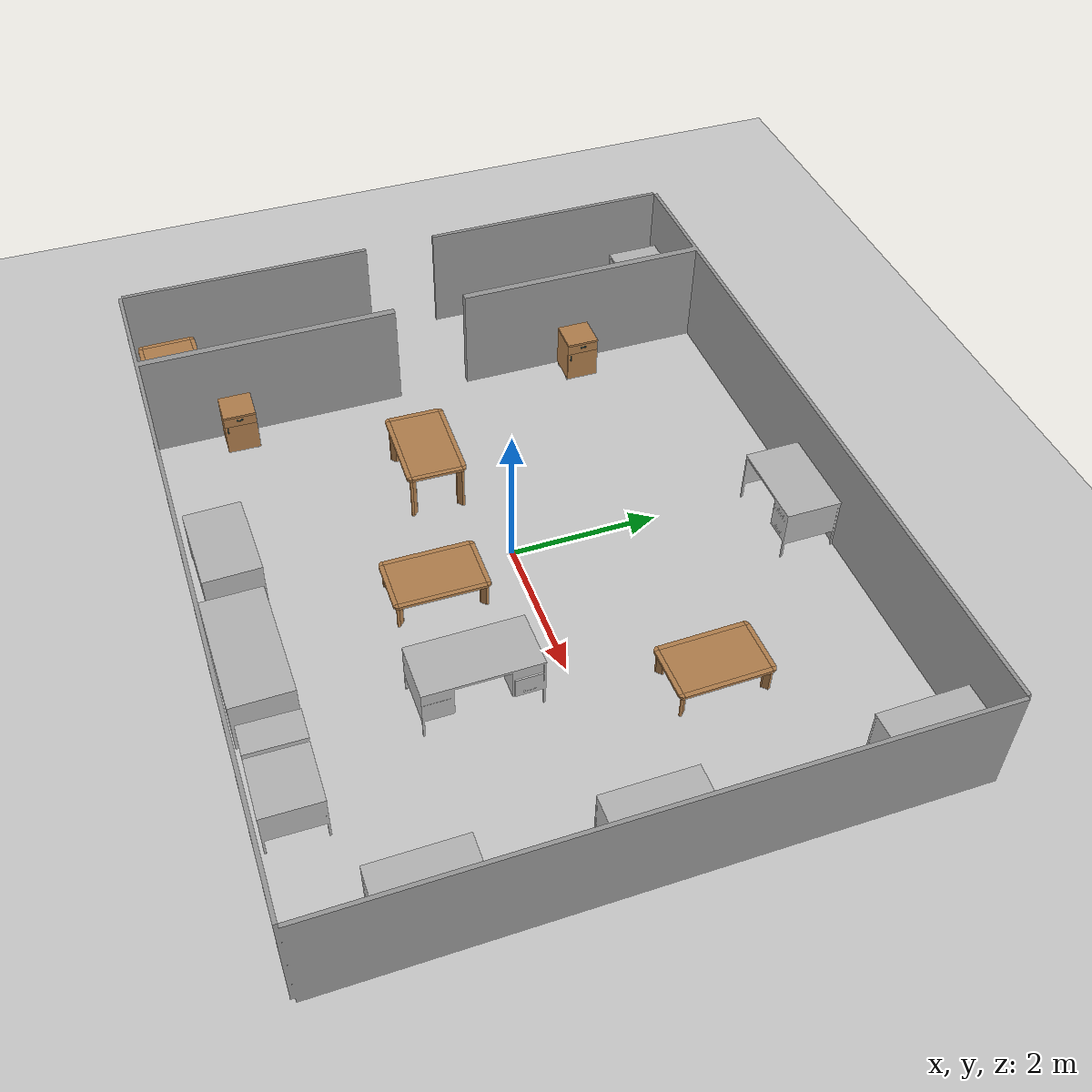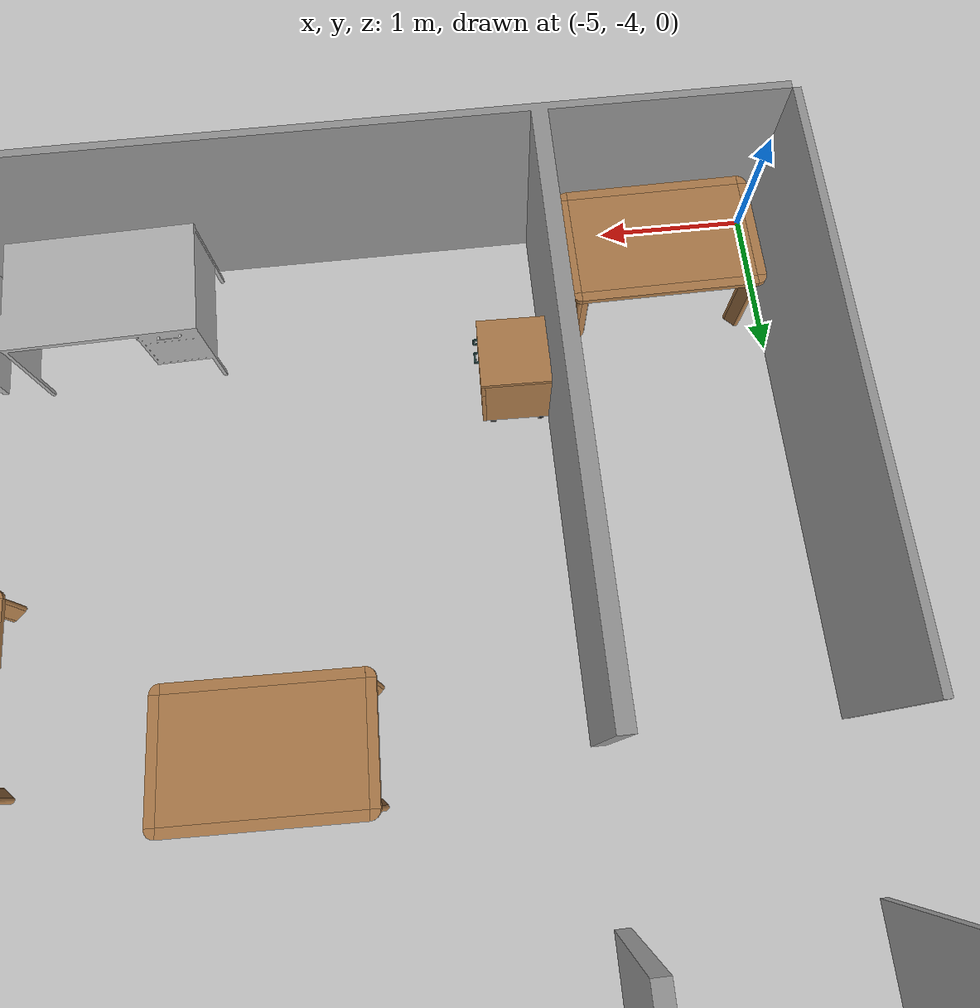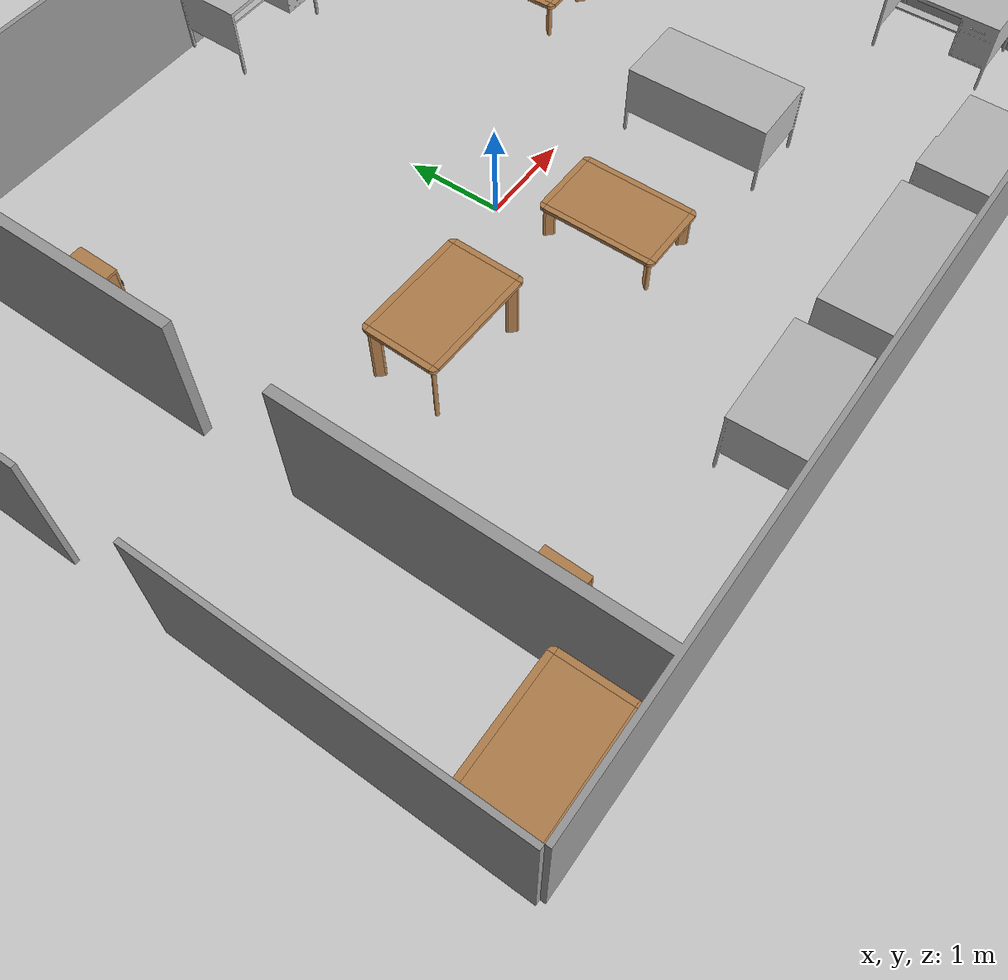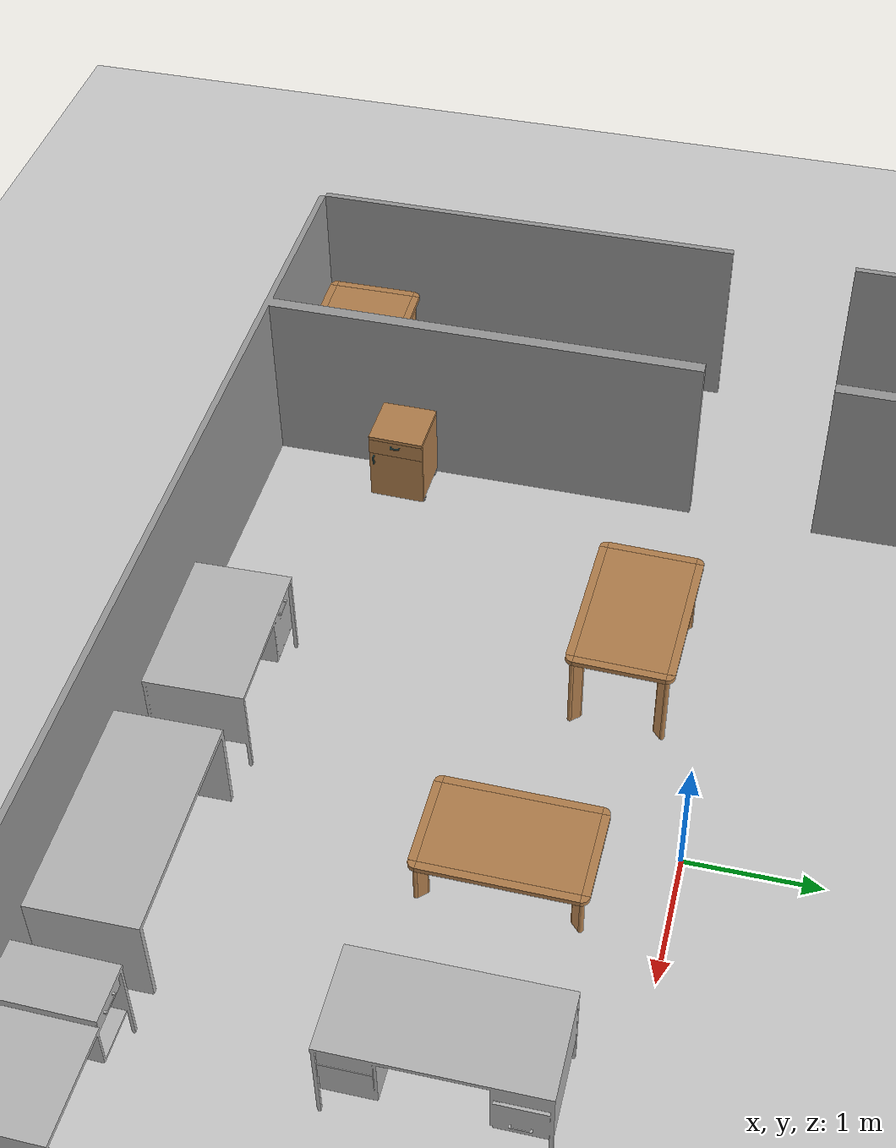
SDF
<sdf version="1.4">
 <world name="default">
  <scene>
   <ambient>0.5 0.5 0.5 1</ambient>
   <shadows>0</shadows>
   <grid>0</grid>
   <background>0.7 0.7 0.7 1</background>
  </scene>
  <physics type="ode">
   <real_time_update_rate>500.0</real_time_update_rate>
   <max_step_size>0.002</max_step_size>
   <ode><solver><type>quick</type><iters>100</iters></solver><constraints><cfm>0.0001</cfm></constraints></ode>
  </physics>
  <light name="user_directional_light_0" type="directional">
   <pose>0 0 5 0 -0 0</pose>
   <diffuse>0.5 0.5 0.5 1</diffuse>
   <specular>0.1 0.1 0.1 1</specular>
   <direction>0.1 0.1 -0.9</direction>
   <attenuation>
    <range>20</range>
    <constant>0.5</constant>
    <linear>0.01</linear>
    <quadratic>0.001</quadratic>
   </attenuation>
  </light>
  <model name="rnd_room_c3_a">
   <link name="link_0">
    <inertial>
     <mass>1</mass>
     <inertia>
      <ixx>0.166667</ixx>
      <ixy>0</ixy>
      <ixz>0</ixz>
      <iyy>0.166667</iyy>
      <iyz>0</iyz>
      <izz>0.166667</izz>
     </inertia>
    </inertial>
    <visual name="visual">
     <geometry><mesh><uri>model://RandomRooms/rnd_room_c2_05.dae</uri><scale>1 1 1</scale></mesh></geometry>
     <material>
      <lighting>1</lighting>
      <script><uri>model://RandomRooms/rnd_room_c2_05.dae</uri><name>Gazebo/Grey</name></script>
      <shader type="pixel"><normal_map>__default__</normal_map></shader>
     </material>
    </visual>
    <collision name="collision">
     <geometry><mesh><uri>model://RandomRooms/rnd_room_c2_05.dae</uri><scale>1 1 1</scale></mesh></geometry>
     <surface>
      <friction>
       <ode><mu>1</mu><mu2>1</mu2><fdir1>0 0 0</fdir1><slip1>0</slip1><slip2>0</slip2></ode>
       <torsional>
        <coefficient>1</coefficient>
        <patch_radius>0</patch_radius>
        <surface_radius>0</surface_radius>
        <use_patch_radius>1</use_patch_radius>
        <ode><slip>0</slip></ode>
       </torsional>
      </friction>
      <bounce><restitution_coefficient>0</restitution_coefficient><threshold>1e+06</threshold></bounce>
      <contact>
       <collide_without_contact>0</collide_without_contact>
       <collide_without_contact_bitmask>1</collide_without_contact_bitmask>
       <collide_bitmask>1</collide_bitmask>
       <ode>
        <soft_cfm>0</soft_cfm>
        <soft_erp>0.2</soft_erp>
        <kp>1e+13</kp>
        <kd>1</kd>
        <max_vel>0.01</max_vel>
        <min_depth>0</min_depth>
       </ode>
       <bullet>
        <split_impulse>1</split_impulse>
        <split_impulse_penetration_threshold>-0.01</split_impulse_penetration_threshold>
        <soft_cfm>0</soft_cfm>
        <soft_erp>0.2</soft_erp>
        <kp>1e+13</kp>
        <kd>1</kd>
       </bullet>
      </contact>
     </surface>
    </collision>
   </link>
   <static>1</static>
  </model>
  <model name="gplane">
   <link name="body">
    <collision name="gplane_coll">
     <geometry><plane><normal>0 0 1</normal><size>25 25</size></plane></geometry>
     <surface><contact><ode><kp>1e+06</kp><kd>1</kd></ode></contact></surface>
     <laser_retro>2000</laser_retro>
    </collision>
    <visual name="gplane_vis">
     <geometry><plane><normal>0 0 1</normal><size>25 25</size></plane></geometry>
     <material>
      <script>
       <uri>model://base_materials/carpet/scripts</uri>
       <uri>model://base_materials/carpet/textures</uri>
       <name>carpet/carpet01</name>
      </script>
     </material>
     <cast_shadows>0</cast_shadows>
    </visual>
    <velocity_decay><linear>0</linear><angular>0</angular></velocity_decay>
   </link>
   <static>1</static>
  </model>
  <model name="Table_02_1">
   <link name="link_0">
    <inertial>
     <mass>15</mass>
     <inertia>
      <ixx>0.166667</ixx>
      <ixy>0</ixy>
      <ixz>0</ixz>
      <iyy>0.166667</iyy>
      <iyz>0</iyz>
      <izz>0.166667</izz>
     </inertia>
    </inertial>
    <visual name="visual">
     <geometry><mesh><uri>model://BioRoboticsLab/meshes/Table_02.dae</uri><scale>1 1 1</scale></mesh></geometry>
     <material><lighting>1</lighting><shader type="pixel"/></material>
    </visual>
    <collision name="collision">
     <geometry><mesh><uri>model://BioRoboticsLab/meshes/Table_02.dae</uri><scale>1 1 1</scale></mesh></geometry>
     <surface>
      <friction>
       <ode><mu>1</mu><mu2>1</mu2><fdir1>0 0 0</fdir1><slip1>0</slip1><slip2>0</slip2></ode>
       <torsional>
        <coefficient>1</coefficient>
        <patch_radius>0</patch_radius>
        <surface_radius>0</surface_radius>
        <use_patch_radius>1</use_patch_radius>
        <ode><slip>0</slip></ode>
       </torsional>
      </friction>
      <bounce><restitution_coefficient>0</restitution_coefficient><threshold>1e+06</threshold></bounce>
      <contact>
       <collide_without_contact>0</collide_without_contact>
       <collide_without_contact_bitmask>1</collide_without_contact_bitmask>
       <collide_bitmask>1</collide_bitmask>
       <ode>
        <soft_cfm>0</soft_cfm>
        <soft_erp>0.2</soft_erp>
        <kp>1e+13</kp>
        <kd>1</kd>
        <max_vel>0.01</max_vel>
        <min_depth>0</min_depth>
       </ode>
       <bullet>
        <split_impulse>1</split_impulse>
        <split_impulse_penetration_threshold>-0.01</split_impulse_penetration_threshold>
        <soft_cfm>0</soft_cfm>
        <soft_erp>0.2</soft_erp>
        <kp>1e+13</kp>
        <kd>1</kd>
       </bullet>
      </contact>
     </surface>
    </collision>
   </link>
   <static>1</static>
   <pose>1.02883 -3.65542 0 0 -0 0.011747</pose>
  </model>
  <model name="Desk_03_1">
   <link name="link_0">
    <inertial>
     <mass>25</mass>
     <inertia>
      <ixx>0.166667</ixx>
      <ixy>0</ixy>
      <ixz>0</ixz>
      <iyy>0.166667</iyy>
      <iyz>0</iyz>
      <izz>0.166667</izz>
     </inertia>
    </inertial>
    <visual name="visual">
     <geometry><mesh><uri>model://BioRoboticsLab/meshes/Desk_03.dae</uri><scale>1 1 1</scale></mesh></geometry>
     <material><lighting>1</lighting><shader type="pixel"/></material>
    </visual>
    <collision name="collision">
     <geometry><mesh><uri>model://BioRoboticsLab/meshes/Desk_03.dae</uri><scale>1 1 1</scale></mesh></geometry>
     <surface>
      <friction>
       <ode><mu>1</mu><mu2>1</mu2><fdir1>0 0 0</fdir1><slip1>0</slip1><slip2>0</slip2></ode>
       <torsional>
        <coefficient>1</coefficient>
        <patch_radius>0</patch_radius>
        <surface_radius>0</surface_radius>
        <use_patch_radius>1</use_patch_radius>
        <ode><slip>0</slip></ode>
       </torsional>
      </friction>
      <bounce><restitution_coefficient>0</restitution_coefficient><threshold>1e+06</threshold></bounce>
      <contact>
       <collide_without_contact>0</collide_without_contact>
       <collide_without_contact_bitmask>1</collide_without_contact_bitmask>
       <collide_bitmask>1</collide_bitmask>
       <ode>
        <soft_cfm>0</soft_cfm>
        <soft_erp>0.2</soft_erp>
        <kp>1e+13</kp>
        <kd>1</kd>
        <max_vel>0.01</max_vel>
        <min_depth>0</min_depth>
       </ode>
       <bullet>
        <split_impulse>1</split_impulse>
        <split_impulse_penetration_threshold>-0.01</split_impulse_penetration_threshold>
        <soft_cfm>0</soft_cfm>
        <soft_erp>0.2</soft_erp>
        <kp>1e+13</kp>
        <kd>1</kd>
       </bullet>
      </contact>
     </surface>
    </collision>
   </link>
   <static>1</static>
   <pose>4.59941 -2.47753 0 0 -0 1.57227</pose>
  </model>
  <model name="kitchen_lowtable_1">
   <link name="link">
    <inertial>
     <mass>10</mass>
     <inertia><ixx>1</ixx><ixy>0</ixy><ixz>0</ixz><iyy>1</iyy><iyz>0</iyz><izz>1</izz></inertia>
    </inertial>
    <visual name="center_board">
     <pose>0 0 0.38 0 -0 0</pose>
     <geometry><box><size>0.68 1.13 0.04</size></box></geometry>
     <material>
      <script><uri>model://base_materials/wood/scripts/wood.material</uri><name>base_materials/wood</name></script>
     </material>
    </visual>
    <collision name="collision_center_board">
     <pose>0 0 0.38 0 -0 0</pose>
     <geometry><box><size>0.68 1.13 0.04</size></box></geometry>
    </collision>
    <visual name="front_board">
     <pose>0.37 0 0.38 0 -0 0</pose>
     <geometry><box><size>0.06 1.13 0.04</size></box></geometry>
     <material>
      <script><uri>model://base_materials/wood/scripts/wood.material</uri><name>base_materials/wood</name></script>
     </material>
    </visual>
    <collision name="collision_front_board">
     <pose>0.37 0 0.38 0 -0 0</pose>
     <geometry><box><size>0.06 1.13 0.04</size></box></geometry>
    </collision>
    <visual name="back_board">
     <pose>-0.37 0 0.38 0 -0 0</pose>
     <geometry><box><size>0.06 1.13 0.04</size></box></geometry>
     <material>
      <script><uri>model://base_materials/wood/scripts/wood.material</uri><name>base_materials/wood</name></script>
     </material>
    </visual>
    <collision name="collision_back_board">
     <pose>-0.37 0 0.38 0 -0 0</pose>
     <geometry><box><size>0.06 1.13 0.04</size></box></geometry>
    </collision>
    <visual name="right_board">
     <pose>0 0.595 0.38 0 -0 0</pose>
     <geometry><box><size>0.68 0.06 0.04</size></box></geometry>
     <material>
      <script><uri>model://base_materials/wood/scripts/wood.material</uri><name>base_materials/wood</name></script>
     </material>
    </visual>
    <collision name="collision_right_board">
     <pose>0 0.595 0.38 0 -0 0</pose>
     <geometry><box><size>0.68 0.06 0.04</size></box></geometry>
    </collision>
    <visual name="left_board">
     <pose>0 -0.595 0.38 0 -0 0</pose>
     <geometry><box><size>0.68 0.06 0.04</size></box></geometry>
     <material>
      <script><uri>model://base_materials/wood/scripts/wood.material</uri><name>base_materials/wood</name></script>
     </material>
    </visual>
    <collision name="collision_left_board">
     <pose>0 -0.595 0.38 0 -0 0</pose>
     <geometry><box><size>0.68 0.06 0.04</size></box></geometry>
    </collision>
    <visual name="front_right_corner_board">
     <pose>0.34 0.565 0.38 0 -0 0</pose>
     <geometry><cylinder><radius>0.06</radius><length>0.039</length></cylinder></geometry>
     <material>
      <script><uri>model://base_materials/wood/scripts/wood.material</uri><name>base_materials/wood</name></script>
     </material>
    </visual>
    <collision name="collision_front_right_corner_board">
     <pose>0.34 0.565 0.38 0 -0 0</pose>
     <geometry><cylinder><radius>0.06</radius><length>0.039</length></cylinder></geometry>
    </collision>
    <visual name="front_left_corner_board">
     <pose>0.34 -0.565 0.38 0 -0 0</pose>
     <geometry><cylinder><radius>0.06</radius><length>0.039</length></cylinder></geometry>
     <material>
      <script><uri>model://base_materials/wood/scripts/wood.material</uri><name>base_materials/wood</name></script>
     </material>
    </visual>
    <collision name="collision_front_left_corner_board">
     <pose>0.34 -0.565 0.38 0 -0 0</pose>
     <geometry><cylinder><radius>0.06</radius><length>0.039</length></cylinder></geometry>
    </collision>
    <visual name="front_back_right_corner_board">
     <pose>-0.34 0.565 0.38 0 -0 0</pose>
     <geometry><cylinder><radius>0.06</radius><length>0.039</length></cylinder></geometry>
     <material>
      <script><uri>model://base_materials/wood/scripts/wood.material</uri><name>base_materials/wood</name></script>
     </material>
    </visual>
    <collision name="collision_back_right_corner_board">
     <pose>-0.34 0.565 0.38 0 -0 0</pose>
     <geometry><cylinder><radius>0.06</radius><length>0.039</length></cylinder></geometry>
    </collision>
    <visual name="front_back_left_corner_board">
     <pose>-0.34 -0.565 0.38 0 -0 0</pose>
     <geometry><cylinder><radius>0.06</radius><length>0.039</length></cylinder></geometry>
     <material>
      <script><uri>model://base_materials/wood/scripts/wood.material</uri><name>base_materials/wood</name></script>
     </material>
    </visual>
    <collision name="collision_back_left_corner_board">
     <pose>-0.34 -0.565 0.38 0 -0 0</pose>
     <geometry><cylinder><radius>0.06</radius><length>0.039</length></cylinder></geometry>
    </collision>
    <visual name="front_left_corner_frame1">
     <pose>0.345858 -0.57086 0.18 0 -0 0</pose>
     <geometry><cylinder><radius>0.02</radius><length>0.36</length></cylinder></geometry>
     <material>
      <script><uri>model://base_materials/wood/scripts/wood.material</uri><name>base_materials/wood</name></script>
     </material>
    </visual>
    <collision name="collision_front_left_corner_frame1">
     <pose>0.345858 -0.57086 0.18 0 -0 0</pose>
     <geometry><cylinder><radius>0.02</radius><length>0.36</length></cylinder></geometry>
    </collision>
    <visual name="front_left_corner_frame2">
     <pose>0.317574 -0.54257 0.18 0 -0 0.7854</pose>
     <geometry><box><size>0.04 0.08 0.36</size></box></geometry>
     <material>
      <script><uri>model://base_materials/wood/scripts/wood.material</uri><name>base_materials/wood</name></script>
     </material>
    </visual>
    <collision name="collision_front_left_corner_frame2">
     <pose>0.317574 -0.54257 0.18 0 -0 0.7854</pose>
     <geometry><box><size>0.04 0.08 0.36</size></box></geometry>
    </collision>
    <visual name="front_left_corner_frame3">
     <pose>0.289289 -0.51429 0.18 0 -0 0</pose>
     <geometry><cylinder><radius>0.02</radius><length>0.36</length></cylinder></geometry>
     <material>
      <script><uri>model://base_materials/wood/scripts/wood.material</uri><name>base_materials/wood</name></script>
     </material>
    </visual>
    <collision name="collision_front_left_corner_frame3">
     <pose>0.289289 -0.51429 0.18 0 -0 0</pose>
     <geometry><cylinder><radius>0.02</radius><length>0.36</length></cylinder></geometry>
    </collision>
    <visual name="front_right_corner_frame1">
     <pose>0.345858 0.57086 0.18 0 -0 0</pose>
     <geometry><cylinder><radius>0.02</radius><length>0.36</length></cylinder></geometry>
     <material>
      <script><uri>model://base_materials/wood/scripts/wood.material</uri><name>base_materials/wood</name></script>
     </material>
    </visual>
    <collision name="collision_front_right_corner_frame1">
     <pose>0.345858 0.57086 0.18 0 -0 0</pose>
     <geometry><cylinder><radius>0.02</radius><length>0.36</length></cylinder></geometry>
    </collision>
    <visual name="front_right_corner_frame2">
     <pose>0.317574 0.54257 0.18 0 0 -0.7854</pose>
     <geometry><box><size>0.04 0.08 0.36</size></box></geometry>
     <material>
      <script><uri>model://base_materials/wood/scripts/wood.material</uri><name>base_materials/wood</name></script>
     </material>
    </visual>
    <collision name="collision_front_right_corner_frame2">
     <pose>0.317574 0.54257 0.18 0 0 -0.7854</pose>
     <geometry><box><size>0.04 0.08 0.36</size></box></geometry>
    </collision>
    <visual name="front_right_corner_frame3">
     <pose>0.289289 0.51429 0.18 0 -0 0</pose>
     <geometry><cylinder><radius>0.02</radius><length>0.36</length></cylinder></geometry>
     <material>
      <script><uri>model://base_materials/wood/scripts/wood.material</uri><name>base_materials/wood</name></script>
     </material>
    </visual>
    <collision name="collision_front_right_corner_frame3">
     <pose>0.289289 0.51429 0.18 0 -0 0</pose>
     <geometry><cylinder><radius>0.02</radius><length>0.36</length></cylinder></geometry>
    </collision>
    <visual name="back_left_corner_frame1">
     <pose>-0.345858 -0.57086 0.18 0 -0 0</pose>
     <geometry><cylinder><radius>0.02</radius><length>0.36</length></cylinder></geometry>
     <material>
      <script><uri>model://base_materials/wood/scripts/wood.material</uri><name>base_materials/wood</name></script>
     </material>
    </visual>
    <collision name="collision_back_left_corner_frame1">
     <pose>-0.345858 -0.57086 0.18 0 -0 0</pose>
     <geometry><cylinder><radius>0.02</radius><length>0.36</length></cylinder></geometry>
    </collision>
    <visual name="back_left_corner_frame2">
     <pose>-0.317574 -0.54257 0.18 0 0 -0.7854</pose>
     <geometry><box><size>0.04 0.08 0.36</size></box></geometry>
     <material>
      <script><uri>model://base_materials/wood/scripts/wood.material</uri><name>base_materials/wood</name></script>
     </material>
    </visual>
    <collision name="collision_back_left_corner_frame2">
     <pose>-0.317574 -0.54257 0.18 0 0 -0.7854</pose>
     <geometry><box><size>0.04 0.08 0.36</size></box></geometry>
    </collision>
    <visual name="back_left_corner_frame3">
     <pose>-0.289289 -0.51429 0.18 0 -0 0</pose>
     <geometry><cylinder><radius>0.02</radius><length>0.36</length></cylinder></geometry>
     <material>
      <script><uri>model://base_materials/wood/scripts/wood.material</uri><name>base_materials/wood</name></script>
     </material>
    </visual>
    <collision name="collision_back_left_corner_frame3">
     <pose>-0.289289 -0.51429 0.18 0 -0 0</pose>
     <geometry><cylinder><radius>0.02</radius><length>0.36</length></cylinder></geometry>
    </collision>
    <visual name="back_right_corner_frame1">
     <pose>-0.345858 0.57086 0.18 0 -0 0</pose>
     <geometry><cylinder><radius>0.02</radius><length>0.36</length></cylinder></geometry>
     <material>
      <script><uri>model://base_materials/wood/scripts/wood.material</uri><name>base_materials/wood</name></script>
     </material>
    </visual>
    <collision name="collision_back_right_corner_frame1">
     <pose>-0.345858 0.57086 0.18 0 -0 0</pose>
     <geometry><cylinder><radius>0.02</radius><length>0.36</length></cylinder></geometry>
    </collision>
    <visual name="back_right_corner_frame2">
     <pose>-0.317574 0.54257 0.18 0 -0 0.7854</pose>
     <geometry><box><size>0.04 0.08 0.36</size></box></geometry>
     <material>
      <script><uri>model://base_materials/wood/scripts/wood.material</uri><name>base_materials/wood</name></script>
     </material>
    </visual>
    <collision name="collision_back_right_corner_frame2">
     <pose>-0.317574 0.54257 0.18 0 -0 0.7854</pose>
     <geometry><box><size>0.04 0.08 0.36</size></box></geometry>
    </collision>
    <visual name="back_right_corner_frame3">
     <pose>-0.289289 0.51429 0.18 0 -0 0</pose>
     <geometry><cylinder><radius>0.02</radius><length>0.36</length></cylinder></geometry>
     <material>
      <script><uri>model://base_materials/wood/scripts/wood.material</uri><name>base_materials/wood</name></script>
     </material>
    </visual>
    <collision name="collision_back_right_corner_frame3">
     <pose>-0.289289 0.51429 0.18 0 -0 0</pose>
     <geometry><cylinder><radius>0.02</radius><length>0.36</length></cylinder></geometry>
    </collision>
    <velocity_decay><linear>0</linear><angular>0</angular></velocity_decay>
   </link>
   <static>1</static>
   <pose>2.71295 1.58666 0 0 0 -3.12456</pose>
  </model>
  <model name="wagon_1">
   <link name="link">
    <inertial>
     <mass>10</mass>
     <inertia><ixx>1</ixx><ixy>0</ixy><ixz>0</ixz><iyy>1</iyy><iyz>0</iyz><izz>1</izz></inertia>
    </inertial>
    <visual name="left_board">
     <pose>-0.2325 0.01 0.345 0 -0 0</pose>
     <geometry><box><size>0.415 0.02 0.59</size></box></geometry>
     <material>
      <script><uri>model://base_materials/wood/scripts/wood.material</uri><name>base_materials/wood</name></script>
     </material>
    </visual>
    <collision name="collision_left_board">
     <pose>-0.2325 0.01 0.345 0 -0 0</pose>
     <geometry><box><size>0.415 0.02 0.59</size></box></geometry>
    </collision>
    <visual name="right_board">
     <pose>-0.2325 0.4325 0.345 0 -0 0</pose>
     <geometry><box><size>0.415 0.02 0.59</size></box></geometry>
     <material>
      <script><uri>model://base_materials/wood/scripts/wood.material</uri><name>base_materials/wood</name></script>
     </material>
    </visual>
    <collision name="collision_right_board">
     <pose>-0.2325 0.4325 0.345 0 -0 0</pose>
     <geometry><box><size>0.415 0.02 0.59</size></box></geometry>
    </collision>
    <visual name="top_board">
     <pose>-0.22 0.2225 0.655 0 -0 0</pose>
     <geometry><box><size>0.44 0.445 0.03</size></box></geometry>
     <material>
      <script><uri>model://base_materials/wood/scripts/wood.material</uri><name>base_materials/wood</name></script>
     </material>
    </visual>
    <collision name="collision_top_board">
     <pose>-0.22 0.2225 0.655 0 -0 0</pose>
     <geometry><box><size>0.44 0.445 0.03</size></box></geometry>
    </collision>
    <visual name="back_board">
     <pose>-0.425 0.2225 0.345 0 -0 0</pose>
     <geometry><box><size>0.02 0.405 0.59</size></box></geometry>
     <material>
      <script><uri>model://base_materials/wood/scripts/wood.material</uri><name>base_materials/wood</name></script>
     </material>
    </visual>
    <collision name="collision_back_board">
     <pose>-0.425 0.2225 0.345 0 -0 0</pose>
     <geometry><box><size>0.02 0.405 0.59</size></box></geometry>
    </collision>
    <visual name="bottom_board">
     <pose>-0.2325 0.2225 0.06 0 -0 0</pose>
     <geometry><box><size>0.415 0.405 0.02</size></box></geometry>
     <material>
      <script><uri>model://base_materials/wood/scripts/wood.material</uri><name>base_materials/wood</name></script>
     </material>
    </visual>
    <collision name="collision_bottom_board">
     <pose>-0.2325 0.2225 0.06 0 -0 0</pose>
     <geometry><box><size>0.415 0.405 0.02</size></box></geometry>
    </collision>
    <visual name="1st_drawer">
     <pose>-0.0125 0.2225 0.57 0 -0 0</pose>
     <geometry><box><size>0.025 0.445 0.14</size></box></geometry>
     <material>
      <script><uri>model://base_materials/wood/scripts/wood.material</uri><name>base_materials/wood</name></script>
     </material>
    </visual>
    <collision name="collision_1st_drawer">
     <pose>-0.0125 0.2225 0.57 0 -0 0</pose>
     <geometry><box><size>0.025 0.445 0.14</size></box></geometry>
    </collision>
    <visual name="1st_drawer_handle_l1">
     <pose>0.0115 0.1895 0.6 3.14159 1.57079 3.14159</pose>
     <geometry><cylinder><radius>0.007</radius><length>0.023</length></cylinder></geometry>
     <material>
      <ambient>0.18431 0.3098 0.3098 1</ambient>
      <diffuse>0.18431 0.3098 0.3098 1</diffuse>
      <specular>0.1 0.1 0.1 1</specular>
     </material>
    </visual>
    <collision name="collision_1st_drawer_handle_l1">
     <pose>0.0115 0.1895 0.6 3.14159 1.57079 3.14159</pose>
     <geometry><cylinder><radius>0.007</radius><length>0.023</length></cylinder></geometry>
    </collision>
    <visual name="1st_drawer_handle_l2">
     <pose>0.023 0.1895 0.6 0 -0 0</pose>
     <geometry><sphere><radius>0.007</radius></sphere></geometry>
     <material>
      <ambient>0.18431 0.3098 0.3098 1</ambient>
      <diffuse>0.18431 0.3098 0.3098 1</diffuse>
      <specular>0.1 0.1 0.1 1</specular>
     </material>
    </visual>
    <collision name="collision_1st_drawer_handle_l2">
     <pose>0.023 0.1895 0.6 0 -0 0</pose>
     <geometry><sphere><radius>0.007</radius></sphere></geometry>
    </collision>
    <visual name="1st_drawer_handle_r1">
     <pose>0.0115 0.2555 0.6 3.14159 1.57079 3.14159</pose>
     <geometry><cylinder><radius>0.007</radius><length>0.023</length></cylinder></geometry>
     <material>
      <ambient>0.18431 0.3098 0.3098 1</ambient>
      <diffuse>0.18431 0.3098 0.3098 1</diffuse>
      <specular>0.1 0.1 0.1 1</specular>
     </material>
    </visual>
    <collision name="collision_1st_drawer_handle_r1">
     <pose>0.0115 0.2555 0.6 3.14159 1.57079 3.14159</pose>
     <geometry><cylinder><radius>0.007</radius><length>0.023</length></cylinder></geometry>
    </collision>
    <visual name="1st_drawer_handle_r2">
     <pose>0.023 0.2555 0.6 0 -0 0</pose>
     <geometry><sphere><radius>0.007</radius></sphere></geometry>
     <material>
      <ambient>0.18431 0.3098 0.3098 1</ambient>
      <diffuse>0.18431 0.3098 0.3098 1</diffuse>
      <specular>0.1 0.1 0.1 1</specular>
     </material>
    </visual>
    <collision name="collision_1st_drawer_handle_r2">
     <pose>0.023 0.2555 0.6 0 -0 0</pose>
     <geometry><sphere><radius>0.007</radius></sphere></geometry>
    </collision>
    <visual name="1st_drawer_handle_center">
     <pose>0.023 0.2225 0.6 1.5708 -0 0</pose>
     <geometry><cylinder><radius>0.007</radius><length>0.066</length></cylinder></geometry>
     <material>
      <ambient>0.18431 0.3098 0.3098 1</ambient>
      <diffuse>0.18431 0.3098 0.3098 1</diffuse>
      <specular>0.1 0.1 0.1 1</specular>
     </material>
    </visual>
    <collision name="collision_1st_drawer_handle_center">
     <pose>0.023 0.2225 0.6 1.5708 -0 0</pose>
     <geometry><cylinder><radius>0.007</radius><length>0.066</length></cylinder></geometry>
    </collision>
    <visual name="2nd_drawer">
     <pose>-0.0125 0.2225 0.275 0 -0 0</pose>
     <geometry><box><size>0.025 0.445 0.45</size></box></geometry>
     <material>
      <script><uri>model://base_materials/wood/scripts/wood.material</uri><name>base_materials/wood</name></script>
     </material>
    </visual>
    <collision name="collision_2nd_drawer">
     <pose>-0.0125 0.2225 0.275 0 -0 0</pose>
     <geometry><box><size>0.025 0.445 0.45</size></box></geometry>
    </collision>
    <visual name="2nd_drawer_handle_top1">
     <pose>0.0115 0.04 0.47 3.14159 1.57079 3.14159</pose>
     <geometry><cylinder><radius>0.007</radius><length>0.023</length></cylinder></geometry>
     <material>
      <ambient>0.18431 0.3098 0.3098 1</ambient>
      <diffuse>0.18431 0.3098 0.3098 1</diffuse>
      <specular>0.1 0.1 0.1 1</specular>
     </material>
    </visual>
    <collision name="collision_2nd_drawer_handle_top1">
     <pose>0.0115 0.04 0.47 3.14159 1.57079 3.14159</pose>
     <geometry><cylinder><radius>0.007</radius><length>0.023</length></cylinder></geometry>
    </collision>
    <visual name="2nd_drawer_handle_top2">
     <pose>0.023 0.04 0.47 0 -0 0</pose>
     <geometry><sphere><radius>0.007</radius></sphere></geometry>
     <material>
      <ambient>0.18431 0.3098 0.3098 1</ambient>
      <diffuse>0.18431 0.3098 0.3098 1</diffuse>
      <specular>0.1 0.1 0.1 1</specular>
     </material>
    </visual>
    <collision name="2nd_drawer_handle_top2">
     <pose>0.023 0.04 0.47 0 -0 0</pose>
     <geometry><sphere><radius>0.007</radius></sphere></geometry>
    </collision>
    <visual name="2nd_drawer_handle_bottom1">
     <pose>0.0115 0.04 0.404 3.14159 1.57079 3.14159</pose>
     <geometry><cylinder><radius>0.007</radius><length>0.023</length></cylinder></geometry>
     <material>
      <ambient>0.18431 0.3098 0.3098 1</ambient>
      <diffuse>0.18431 0.3098 0.3098 1</diffuse>
      <specular>0.1 0.1 0.1 1</specular>
     </material>
    </visual>
    <collision name="collision_2nd_drawer_handle_bottom1">
     <pose>0.0115 0.04 0.404 3.14159 1.57079 3.14159</pose>
     <geometry><cylinder><radius>0.007</radius><length>0.023</length></cylinder></geometry>
    </collision>
    <visual name="2nd_drawer_handle_bottom2">
     <pose>0.023 0.04 0.404 0 -0 0</pose>
     <geometry><sphere><radius>0.007</radius></sphere></geometry>
     <material>
      <ambient>0.18431 0.3098 0.3098 1</ambient>
      <diffuse>0.18431 0.3098 0.3098 1</diffuse>
      <specular>0.1 0.1 0.1 1</specular>
     </material>
    </visual>
    <collision name="2nd_drawer_handle_bottom2">
     <pose>0.023 0.04 0.404 0 -0 0</pose>
     <geometry><sphere><radius>0.007</radius></sphere></geometry>
    </collision>
    <visual name="2nd_drawer_handle_center">
     <pose>0.023 0.04 0.437 0 -0 0</pose>
     <geometry><cylinder><radius>0.007</radius><length>0.066</length></cylinder></geometry>
     <material>
      <ambient>0.18431 0.3098 0.3098 1</ambient>
      <diffuse>0.18431 0.3098 0.3098 1</diffuse>
      <specular>0.1 0.1 0.1 1</specular>
     </material>
    </visual>
    <collision name="collision_2nd_drawer_handle_center">
     <pose>0.023 0.04 0.437 0 -0 0</pose>
     <geometry><cylinder><radius>0.007</radius><length>0.066</length></cylinder></geometry>
    </collision>
    <visual name="left_front_caster">
     <pose>-0.07 0.025 0.025 3.14159 1.57079 3.14159</pose>
     <geometry><cylinder><radius>0.025</radius><length>0.035</length></cylinder></geometry>
     <material><script><name>Gazebo/Black</name><uri>__default__</uri></script></material>
    </visual>
    <collision name="collision_left_front_caster">
     <pose>-0.07 0.025 0.025 3.14159 1.57079 3.14159</pose>
     <geometry><cylinder><radius>0.025</radius><length>0.035</length></cylinder></geometry>
    </collision>
    <visual name="right_front_caster">
     <pose>-0.07 0.42 0.025 3.14159 1.57079 3.14159</pose>
     <geometry><cylinder><radius>0.025</radius><length>0.035</length></cylinder></geometry>
     <material><script><name>Gazebo/Black</name><uri>__default__</uri></script></material>
    </visual>
    <collision name="collision_right_front_caster">
     <pose>-0.07 0.42 0.025 3.14159 1.57079 3.14159</pose>
     <geometry><cylinder><radius>0.025</radius><length>0.035</length></cylinder></geometry>
    </collision>
    <visual name="left_back_caster">
     <pose>-0.39 0.025 0.025 3.14159 1.57079 3.14159</pose>
     <geometry><cylinder><radius>0.025</radius><length>0.035</length></cylinder></geometry>
     <material><script><name>Gazebo/Black</name><uri>__default__</uri></script></material>
    </visual>
    <collision name="collision_left_back_caster">
     <pose>-0.39 0.025 0.025 3.14159 1.57079 3.14159</pose>
     <geometry><cylinder><radius>0.025</radius><length>0.035</length></cylinder></geometry>
    </collision>
    <visual name="right_back_caster">
     <pose>-0.39 0.42 0.025 3.14159 1.57079 3.14159</pose>
     <geometry><cylinder><radius>0.025</radius><length>0.035</length></cylinder></geometry>
     <material><script><name>Gazebo/Black</name><uri>__default__</uri></script></material>
    </visual>
    <collision name="collision_right_back_caster">
     <pose>-0.39 0.42 0.025 3.14159 1.57079 3.14159</pose>
     <geometry><cylinder><radius>0.025</radius><length>0.035</length></cylinder></geometry>
    </collision>
    <velocity_decay><linear>0</linear><angular>0</angular></velocity_decay>
   </link>
   <static>1</static>
   <pose>-2.96452 1.87957 0 0 0 -0.010136</pose>
  </model>
  <model name="Desk_03_2">
   <link name="link_0">
    <inertial>
     <mass>25</mass>
     <inertia>
      <ixx>0.166667</ixx>
      <ixy>0</ixy>
      <ixz>0</ixz>
      <iyy>0.166667</iyy>
      <iyz>0</iyz>
      <izz>0.166667</izz>
     </inertia>
    </inertial>
    <visual name="visual">
     <geometry><mesh><uri>model://BioRoboticsLab/meshes/Desk_03.dae</uri><scale>1 1 1</scale></mesh></geometry>
     <material><lighting>1</lighting><shader type="pixel"/></material>
    </visual>
    <collision name="collision">
     <geometry><mesh><uri>model://BioRoboticsLab/meshes/Desk_03.dae</uri><scale>1 1 1</scale></mesh></geometry>
     <surface>
      <friction>
       <ode><mu>1</mu><mu2>1</mu2><fdir1>0 0 0</fdir1><slip1>0</slip1><slip2>0</slip2></ode>
       <torsional>
        <coefficient>1</coefficient>
        <patch_radius>0</patch_radius>
        <surface_radius>0</surface_radius>
        <use_patch_radius>1</use_patch_radius>
        <ode><slip>0</slip></ode>
       </torsional>
      </friction>
      <bounce><restitution_coefficient>0</restitution_coefficient><threshold>1e+06</threshold></bounce>
      <contact>
       <collide_without_contact>0</collide_without_contact>
       <collide_without_contact_bitmask>1</collide_without_contact_bitmask>
       <collide_bitmask>1</collide_bitmask>
       <ode>
        <soft_cfm>0</soft_cfm>
        <soft_erp>0.2</soft_erp>
        <kp>1e+13</kp>
        <kd>1</kd>
        <max_vel>0.01</max_vel>
        <min_depth>0</min_depth>
       </ode>
       <bullet>
        <split_impulse>1</split_impulse>
        <split_impulse_penetration_threshold>-0.01</split_impulse_penetration_threshold>
        <soft_cfm>0</soft_cfm>
        <soft_erp>0.2</soft_erp>
        <kp>1e+13</kp>
        <kd>1</kd>
       </bullet>
      </contact>
     </surface>
    </collision>
   </link>
   <static>1</static>
   <pose>4.59987 0.082776 0 0 -0 1.57272</pose>
  </model>
  <model name="Desk_04_1">
   <link name="link_0">
    <inertial>
     <mass>15</mass>
     <inertia>
      <ixx>0.166667</ixx>
      <ixy>0</ixy>
      <ixz>0</ixz>
      <iyy>0.166667</iyy>
      <iyz>0</iyz>
      <izz>0.166667</izz>
     </inertia>
    </inertial>
    <visual name="visual">
     <geometry><mesh><uri>model://BioRoboticsLab/meshes/Desk_04.dae</uri><scale>1 1 1</scale></mesh></geometry>
     <material><lighting>1</lighting><shader type="pixel"/></material>
    </visual>
    <collision name="collision">
     <geometry><mesh><uri>model://BioRoboticsLab/meshes/Desk_04.dae</uri><scale>1 1 1</scale></mesh></geometry>
     <surface>
      <friction>
       <ode><mu>1</mu><mu2>1</mu2><fdir1>0 0 0</fdir1><slip1>0</slip1><slip2>0</slip2></ode>
       <torsional>
        <coefficient>1</coefficient>
        <patch_radius>0</patch_radius>
        <surface_radius>0</surface_radius>
        <use_patch_radius>1</use_patch_radius>
        <ode><slip>0</slip></ode>
       </torsional>
      </friction>
      <bounce><restitution_coefficient>0</restitution_coefficient><threshold>1e+06</threshold></bounce>
      <contact>
       <collide_without_contact>0</collide_without_contact>
       <collide_without_contact_bitmask>1</collide_without_contact_bitmask>
       <collide_bitmask>1</collide_bitmask>
       <ode>
        <soft_cfm>0</soft_cfm>
        <soft_erp>0.2</soft_erp>
        <kp>1e+13</kp>
        <kd>1</kd>
        <max_vel>0.01</max_vel>
        <min_depth>0</min_depth>
       </ode>
       <bullet>
        <split_impulse>1</split_impulse>
        <split_impulse_penetration_threshold>-0.01</split_impulse_penetration_threshold>
        <soft_cfm>0</soft_cfm>
        <soft_erp>0.2</soft_erp>
        <kp>1e+13</kp>
        <kd>1</kd>
       </bullet>
      </contact>
     </surface>
    </collision>
   </link>
   <static>1</static>
   <pose>4.61255 3.37689 0 0 -0 1.58356</pose>
  </model>
  <model name="Desk_02_1">
   <link name="link_0">
    <inertial>
     <mass>19</mass>
     <inertia>
      <ixx>0.166667</ixx>
      <ixy>0</ixy>
      <ixz>0</ixz>
      <iyy>0.166667</iyy>
      <iyz>0</iyz>
      <izz>0.166667</izz>
     </inertia>
    </inertial>
    <visual name="visual">
     <geometry><mesh><uri>model://BioRoboticsLab/meshes/Desk_02.dae</uri><scale>1 1 1</scale></mesh></geometry>
     <material><lighting>1</lighting><shader type="pixel"/></material>
    </visual>
    <collision name="collision">
     <geometry><mesh><uri>model://BioRoboticsLab/meshes/Desk_02.dae</uri><scale>1 1 1</scale></mesh></geometry>
     <surface>
      <friction>
       <ode><mu>1</mu><mu2>1</mu2><fdir1>0 0 0</fdir1><slip1>0</slip1><slip2>0</slip2></ode>
       <torsional>
        <coefficient>1</coefficient>
        <patch_radius>0</patch_radius>
        <surface_radius>0</surface_radius>
        <use_patch_radius>1</use_patch_radius>
        <ode><slip>0</slip></ode>
       </torsional>
      </friction>
      <bounce><restitution_coefficient>0</restitution_coefficient><threshold>1e+06</threshold></bounce>
      <contact>
       <collide_without_contact>0</collide_without_contact>
       <collide_without_contact_bitmask>1</collide_without_contact_bitmask>
       <collide_bitmask>1</collide_bitmask>
       <ode>
        <soft_cfm>0</soft_cfm>
        <soft_erp>0.2</soft_erp>
        <kp>1e+13</kp>
        <kd>1</kd>
        <max_vel>0.01</max_vel>
        <min_depth>0</min_depth>
       </ode>
       <bullet>
        <split_impulse>1</split_impulse>
        <split_impulse_penetration_threshold>-0.01</split_impulse_penetration_threshold>
        <soft_cfm>0</soft_cfm>
        <soft_erp>0.2</soft_erp>
        <kp>1e+13</kp>
        <kd>1</kd>
       </bullet>
      </contact>
     </surface>
    </collision>
   </link>
   <static>1</static>
   <pose>2.56399 -3.5685 0 0 0 -0.01062</pose>
  </model>
  <model name="Desk_01_1">
   <link name="link_0">
    <inertial>
     <mass>35</mass>
     <inertia>
      <ixx>0.166667</ixx>
      <ixy>0</ixy>
      <ixz>0</ixz>
      <iyy>0.166667</iyy>
      <iyz>0</iyz>
      <izz>0.166667</izz>
     </inertia>
    </inertial>
    <visual name="visual">
     <geometry><mesh><uri>model://BioRoboticsLab/meshes/Desk_01.dae</uri><scale>1 1 1</scale></mesh></geometry>
     <material><lighting>1</lighting><shader type="pixel"/></material>
    </visual>
    <collision name="collision">
     <geometry><mesh><uri>model://BioRoboticsLab/meshes/Desk_01.dae</uri><scale>1 1 1</scale></mesh></geometry>
     <surface>
      <friction>
       <ode><mu>1</mu><mu2>1</mu2><fdir1>0 0 0</fdir1><slip1>0</slip1><slip2>0</slip2></ode>
       <torsional>
        <coefficient>1</coefficient>
        <patch_radius>0</patch_radius>
        <surface_radius>0</surface_radius>
        <use_patch_radius>1</use_patch_radius>
        <ode><slip>0</slip></ode>
       </torsional>
      </friction>
      <bounce><restitution_coefficient>0</restitution_coefficient><threshold>1e+06</threshold></bounce>
      <contact>
       <collide_without_contact>0</collide_without_contact>
       <collide_without_contact_bitmask>1</collide_without_contact_bitmask>
       <collide_bitmask>1</collide_bitmask>
       <ode>
        <soft_cfm>0</soft_cfm>
        <soft_erp>0.2</soft_erp>
        <kp>1e+13</kp>
        <kd>1</kd>
        <max_vel>0.01</max_vel>
        <min_depth>0</min_depth>
       </ode>
       <bullet>
        <split_impulse>1</split_impulse>
        <split_impulse_penetration_threshold>-0.01</split_impulse_penetration_threshold>
        <soft_cfm>0</soft_cfm>
        <soft_erp>0.2</soft_erp>
        <kp>1e+13</kp>
        <kd>1</kd>
       </bullet>
      </contact>
     </surface>
    </collision>
   </link>
   <static>1</static>
   <pose>2.01759 -1.15148 -0 0 0 -1.56468</pose>
  </model>
  <model name="Desk_02_2">
   <link name="link_0">
    <inertial>
     <mass>19</mass>
     <inertia>
      <ixx>0.166667</ixx>
      <ixy>0</ixy>
      <ixz>0</ixz>
      <iyy>0.166667</iyy>
      <iyz>0</iyz>
      <izz>0.166667</izz>
     </inertia>
    </inertial>
    <visual name="visual">
     <geometry><mesh><uri>model://BioRoboticsLab/meshes/Desk_02.dae</uri><scale>1 1 1</scale></mesh></geometry>
     <material><lighting>1</lighting><shader type="pixel"/></material>
    </visual>
    <collision name="collision">
     <geometry><mesh><uri>model://BioRoboticsLab/meshes/Desk_02.dae</uri><scale>1 1 1</scale></mesh></geometry>
     <surface>
      <friction>
       <ode><mu>1</mu><mu2>1</mu2><fdir1>0 0 0</fdir1><slip1>0</slip1><slip2>0</slip2></ode>
       <torsional>
        <coefficient>1</coefficient>
        <patch_radius>0</patch_radius>
        <surface_radius>0</surface_radius>
        <use_patch_radius>1</use_patch_radius>
        <ode><slip>0</slip></ode>
       </torsional>
      </friction>
      <bounce><restitution_coefficient>0</restitution_coefficient><threshold>1e+06</threshold></bounce>
      <contact>
       <collide_without_contact>0</collide_without_contact>
       <collide_without_contact_bitmask>1</collide_without_contact_bitmask>
       <collide_bitmask>1</collide_bitmask>
       <ode>
        <soft_cfm>0</soft_cfm>
        <soft_erp>0.2</soft_erp>
        <kp>1e+13</kp>
        <kd>1</kd>
        <max_vel>0.01</max_vel>
        <min_depth>0</min_depth>
       </ode>
       <bullet>
        <split_impulse>1</split_impulse>
        <split_impulse_penetration_threshold>-0.01</split_impulse_penetration_threshold>
        <soft_cfm>0</soft_cfm>
        <soft_erp>0.2</soft_erp>
        <kp>1e+13</kp>
        <kd>1</kd>
       </bullet>
      </contact>
     </surface>
    </collision>
   </link>
   <static>1</static>
   <pose>-4.08026 3.62197 0 0 -0 3.13995</pose>
  </model>
  <model name="kitchen_lowtable_2">
   <link name="link">
    <inertial>
     <mass>10</mass>
     <inertia><ixx>1</ixx><ixy>0</ixy><ixz>0</ixz><iyy>1</iyy><iyz>0</iyz><izz>1</izz></inertia>
    </inertial>
    <visual name="center_board">
     <pose>0 0 0.38 0 -0 0</pose>
     <geometry><box><size>0.68 1.13 0.04</size></box></geometry>
     <material>
      <script><uri>model://base_materials/wood/scripts/wood.material</uri><name>base_materials/wood</name></script>
     </material>
    </visual>
    <collision name="collision_center_board">
     <pose>0 0 0.38 0 -0 0</pose>
     <geometry><box><size>0.68 1.13 0.04</size></box></geometry>
    </collision>
    <visual name="front_board">
     <pose>0.37 0 0.38 0 -0 0</pose>
     <geometry><box><size>0.06 1.13 0.04</size></box></geometry>
     <material>
      <script><uri>model://base_materials/wood/scripts/wood.material</uri><name>base_materials/wood</name></script>
     </material>
    </visual>
    <collision name="collision_front_board">
     <pose>0.37 0 0.38 0 -0 0</pose>
     <geometry><box><size>0.06 1.13 0.04</size></box></geometry>
    </collision>
    <visual name="back_board">
     <pose>-0.37 0 0.38 0 -0 0</pose>
     <geometry><box><size>0.06 1.13 0.04</size></box></geometry>
     <material>
      <script><uri>model://base_materials/wood/scripts/wood.material</uri><name>base_materials/wood</name></script>
     </material>
    </visual>
    <collision name="collision_back_board">
     <pose>-0.37 0 0.38 0 -0 0</pose>
     <geometry><box><size>0.06 1.13 0.04</size></box></geometry>
    </collision>
    <visual name="right_board">
     <pose>0 0.595 0.38 0 -0 0</pose>
     <geometry><box><size>0.68 0.06 0.04</size></box></geometry>
     <material>
      <script><uri>model://base_materials/wood/scripts/wood.material</uri><name>base_materials/wood</name></script>
     </material>
    </visual>
    <collision name="collision_right_board">
     <pose>0 0.595 0.38 0 -0 0</pose>
     <geometry><box><size>0.68 0.06 0.04</size></box></geometry>
    </collision>
    <visual name="left_board">
     <pose>0 -0.595 0.38 0 -0 0</pose>
     <geometry><box><size>0.68 0.06 0.04</size></box></geometry>
     <material>
      <script><uri>model://base_materials/wood/scripts/wood.material</uri><name>base_materials/wood</name></script>
     </material>
    </visual>
    <collision name="collision_left_board">
     <pose>0 -0.595 0.38 0 -0 0</pose>
     <geometry><box><size>0.68 0.06 0.04</size></box></geometry>
    </collision>
    <visual name="front_right_corner_board">
     <pose>0.34 0.565 0.38 0 -0 0</pose>
     <geometry><cylinder><radius>0.06</radius><length>0.039</length></cylinder></geometry>
     <material>
      <script><uri>model://base_materials/wood/scripts/wood.material</uri><name>base_materials/wood</name></script>
     </material>
    </visual>
    <collision name="collision_front_right_corner_board">
     <pose>0.34 0.565 0.38 0 -0 0</pose>
     <geometry><cylinder><radius>0.06</radius><length>0.039</length></cylinder></geometry>
    </collision>
    <visual name="front_left_corner_board">
     <pose>0.34 -0.565 0.38 0 -0 0</pose>
     <geometry><cylinder><radius>0.06</radius><length>0.039</length></cylinder></geometry>
     <material>
      <script><uri>model://base_materials/wood/scripts/wood.material</uri><name>base_materials/wood</name></script>
     </material>
    </visual>
    <collision name="collision_front_left_corner_board">
     <pose>0.34 -0.565 0.38 0 -0 0</pose>
     <geometry><cylinder><radius>0.06</radius><length>0.039</length></cylinder></geometry>
    </collision>
    <visual name="front_back_right_corner_board">
     <pose>-0.34 0.565 0.38 0 -0 0</pose>
     <geometry><cylinder><radius>0.06</radius><length>0.039</length></cylinder></geometry>
     <material>
      <script><uri>model://base_materials/wood/scripts/wood.material</uri><name>base_materials/wood</name></script>
     </material>
    </visual>
    <collision name="collision_back_right_corner_board">
     <pose>-0.34 0.565 0.38 0 -0 0</pose>
     <geometry><cylinder><radius>0.06</radius><length>0.039</length></cylinder></geometry>
    </collision>
    <visual name="front_back_left_corner_board">
     <pose>-0.34 -0.565 0.38 0 -0 0</pose>
     <geometry><cylinder><radius>0.06</radius><length>0.039</length></cylinder></geometry>
     <material>
      <script><uri>model://base_materials/wood/scripts/wood.material</uri><name>base_materials/wood</name></script>
     </material>
    </visual>
    <collision name="collision_back_left_corner_board">
     <pose>-0.34 -0.565 0.38 0 -0 0</pose>
     <geometry><cylinder><radius>0.06</radius><length>0.039</length></cylinder></geometry>
    </collision>
    <visual name="front_left_corner_frame1">
     <pose>0.345858 -0.57086 0.18 0 -0 0</pose>
     <geometry><cylinder><radius>0.02</radius><length>0.36</length></cylinder></geometry>
     <material>
      <script><uri>model://base_materials/wood/scripts/wood.material</uri><name>base_materials/wood</name></script>
     </material>
    </visual>
    <collision name="collision_front_left_corner_frame1">
     <pose>0.345858 -0.57086 0.18 0 -0 0</pose>
     <geometry><cylinder><radius>0.02</radius><length>0.36</length></cylinder></geometry>
    </collision>
    <visual name="front_left_corner_frame2">
     <pose>0.317574 -0.54257 0.18 0 -0 0.7854</pose>
     <geometry><box><size>0.04 0.08 0.36</size></box></geometry>
     <material>
      <script><uri>model://base_materials/wood/scripts/wood.material</uri><name>base_materials/wood</name></script>
     </material>
    </visual>
    <collision name="collision_front_left_corner_frame2">
     <pose>0.317574 -0.54257 0.18 0 -0 0.7854</pose>
     <geometry><box><size>0.04 0.08 0.36</size></box></geometry>
    </collision>
    <visual name="front_left_corner_frame3">
     <pose>0.289289 -0.51429 0.18 0 -0 0</pose>
     <geometry><cylinder><radius>0.02</radius><length>0.36</length></cylinder></geometry>
     <material>
      <script><uri>model://base_materials/wood/scripts/wood.material</uri><name>base_materials/wood</name></script>
     </material>
    </visual>
    <collision name="collision_front_left_corner_frame3">
     <pose>0.289289 -0.51429 0.18 0 -0 0</pose>
     <geometry><cylinder><radius>0.02</radius><length>0.36</length></cylinder></geometry>
    </collision>
    <visual name="front_right_corner_frame1">
     <pose>0.345858 0.57086 0.18 0 -0 0</pose>
     <geometry><cylinder><radius>0.02</radius><length>0.36</length></cylinder></geometry>
     <material>
      <script><uri>model://base_materials/wood/scripts/wood.material</uri><name>base_materials/wood</name></script>
     </material>
    </visual>
    <collision name="collision_front_right_corner_frame1">
     <pose>0.345858 0.57086 0.18 0 -0 0</pose>
     <geometry><cylinder><radius>0.02</radius><length>0.36</length></cylinder></geometry>
    </collision>
    <visual name="front_right_corner_frame2">
     <pose>0.317574 0.54257 0.18 0 0 -0.7854</pose>
     <geometry><box><size>0.04 0.08 0.36</size></box></geometry>
     <material>
      <script><uri>model://base_materials/wood/scripts/wood.material</uri><name>base_materials/wood</name></script>
     </material>
    </visual>
    <collision name="collision_front_right_corner_frame2">
     <pose>0.317574 0.54257 0.18 0 0 -0.7854</pose>
     <geometry><box><size>0.04 0.08 0.36</size></box></geometry>
    </collision>
    <visual name="front_right_corner_frame3">
     <pose>0.289289 0.51429 0.18 0 -0 0</pose>
     <geometry><cylinder><radius>0.02</radius><length>0.36</length></cylinder></geometry>
     <material>
      <script><uri>model://base_materials/wood/scripts/wood.material</uri><name>base_materials/wood</name></script>
     </material>
    </visual>
    <collision name="collision_front_right_corner_frame3">
     <pose>0.289289 0.51429 0.18 0 -0 0</pose>
     <geometry><cylinder><radius>0.02</radius><length>0.36</length></cylinder></geometry>
    </collision>
    <visual name="back_left_corner_frame1">
     <pose>-0.345858 -0.57086 0.18 0 -0 0</pose>
     <geometry><cylinder><radius>0.02</radius><length>0.36</length></cylinder></geometry>
     <material>
      <script><uri>model://base_materials/wood/scripts/wood.material</uri><name>base_materials/wood</name></script>
     </material>
    </visual>
    <collision name="collision_back_left_corner_frame1">
     <pose>-0.345858 -0.57086 0.18 0 -0 0</pose>
     <geometry><cylinder><radius>0.02</radius><length>0.36</length></cylinder></geometry>
    </collision>
    <visual name="back_left_corner_frame2">
     <pose>-0.317574 -0.54257 0.18 0 0 -0.7854</pose>
     <geometry><box><size>0.04 0.08 0.36</size></box></geometry>
     <material>
      <script><uri>model://base_materials/wood/scripts/wood.material</uri><name>base_materials/wood</name></script>
     </material>
    </visual>
    <collision name="collision_back_left_corner_frame2">
     <pose>-0.317574 -0.54257 0.18 0 0 -0.7854</pose>
     <geometry><box><size>0.04 0.08 0.36</size></box></geometry>
    </collision>
    <visual name="back_left_corner_frame3">
     <pose>-0.289289 -0.51429 0.18 0 -0 0</pose>
     <geometry><cylinder><radius>0.02</radius><length>0.36</length></cylinder></geometry>
     <material>
      <script><uri>model://base_materials/wood/scripts/wood.material</uri><name>base_materials/wood</name></script>
     </material>
    </visual>
    <collision name="collision_back_left_corner_frame3">
     <pose>-0.289289 -0.51429 0.18 0 -0 0</pose>
     <geometry><cylinder><radius>0.02</radius><length>0.36</length></cylinder></geometry>
    </collision>
    <visual name="back_right_corner_frame1">
     <pose>-0.345858 0.57086 0.18 0 -0 0</pose>
     <geometry><cylinder><radius>0.02</radius><length>0.36</length></cylinder></geometry>
     <material>
      <script><uri>model://base_materials/wood/scripts/wood.material</uri><name>base_materials/wood</name></script>
     </material>
    </visual>
    <collision name="collision_back_right_corner_frame1">
     <pose>-0.345858 0.57086 0.18 0 -0 0</pose>
     <geometry><cylinder><radius>0.02</radius><length>0.36</length></cylinder></geometry>
    </collision>
    <visual name="back_right_corner_frame2">
     <pose>-0.317574 0.54257 0.18 0 -0 0.7854</pose>
     <geometry><box><size>0.04 0.08 0.36</size></box></geometry>
     <material>
      <script><uri>model://base_materials/wood/scripts/wood.material</uri><name>base_materials/wood</name></script>
     </material>
    </visual>
    <collision name="collision_back_right_corner_frame2">
     <pose>-0.317574 0.54257 0.18 0 -0 0.7854</pose>
     <geometry><box><size>0.04 0.08 0.36</size></box></geometry>
    </collision>
    <visual name="back_right_corner_frame3">
     <pose>-0.289289 0.51429 0.18 0 -0 0</pose>
     <geometry><cylinder><radius>0.02</radius><length>0.36</length></cylinder></geometry>
     <material>
      <script><uri>model://base_materials/wood/scripts/wood.material</uri><name>base_materials/wood</name></script>
     </material>
    </visual>
    <collision name="collision_back_right_corner_frame3">
     <pose>-0.289289 0.51429 0.18 0 -0 0</pose>
     <geometry><cylinder><radius>0.02</radius><length>0.36</length></cylinder></geometry>
    </collision>
    <velocity_decay><linear>0</linear><angular>0</angular></velocity_decay>
   </link>
   <static>1</static>
   <pose>0.362122 -1.13503 -0 0 -0 3.1351</pose>
  </model>
  <model name="Desk_03_3">
   <link name="link_0">
    <inertial>
     <mass>25</mass>
     <inertia>
      <ixx>0.166667</ixx>
      <ixy>0</ixy>
      <ixz>0</ixz>
      <iyy>0.166667</iyy>
      <iyz>0</iyz>
      <izz>0.166667</izz>
     </inertia>
    </inertial>
    <visual name="visual">
     <geometry><mesh><uri>model://BioRoboticsLab/meshes/Desk_03.dae</uri><scale>1 1 1</scale></mesh></geometry>
     <material><lighting>1</lighting><shader type="pixel"/></material>
    </visual>
    <collision name="collision">
     <geometry><mesh><uri>model://BioRoboticsLab/meshes/Desk_03.dae</uri><scale>1 1 1</scale></mesh></geometry>
     <surface>
      <friction>
       <ode><mu>1</mu><mu2>1</mu2><fdir1>0 0 0</fdir1><slip1>0</slip1><slip2>0</slip2></ode>
       <torsional>
        <coefficient>1</coefficient>
        <patch_radius>0</patch_radius>
        <surface_radius>0</surface_radius>
        <use_patch_radius>1</use_patch_radius>
        <ode><slip>0</slip></ode>
       </torsional>
      </friction>
      <bounce><restitution_coefficient>0</restitution_coefficient><threshold>1e+06</threshold></bounce>
      <contact>
       <collide_without_contact>0</collide_without_contact>
       <collide_without_contact_bitmask>1</collide_without_contact_bitmask>
       <collide_bitmask>1</collide_bitmask>
       <ode>
        <soft_cfm>0</soft_cfm>
        <soft_erp>0.2</soft_erp>
        <kp>1e+13</kp>
        <kd>1</kd>
        <max_vel>0.01</max_vel>
        <min_depth>0</min_depth>
       </ode>
       <bullet>
        <split_impulse>1</split_impulse>
        <split_impulse_penetration_threshold>-0.01</split_impulse_penetration_threshold>
        <soft_cfm>0</soft_cfm>
        <soft_erp>0.2</soft_erp>
        <kp>1e+13</kp>
        <kd>1</kd>
       </bullet>
      </contact>
     </surface>
    </collision>
   </link>
   <static>1</static>
   <pose>-0.686555 -3.53859 -0 0 -0 0.023926</pose>
  </model>
  <model name="wagon_2">
   <link name="link">
    <inertial>
     <mass>10</mass>
     <inertia><ixx>1</ixx><ixy>0</ixy><ixz>0</ixz><iyy>1</iyy><iyz>0</iyz><izz>1</izz></inertia>
    </inertial>
    <visual name="left_board">
     <pose>-0.2325 0.01 0.345 0 -0 0</pose>
     <geometry><box><size>0.415 0.02 0.59</size></box></geometry>
     <material>
      <script><uri>model://base_materials/wood/scripts/wood.material</uri><name>base_materials/wood</name></script>
     </material>
    </visual>
    <collision name="collision_left_board">
     <pose>-0.2325 0.01 0.345 0 -0 0</pose>
     <geometry><box><size>0.415 0.02 0.59</size></box></geometry>
    </collision>
    <visual name="right_board">
     <pose>-0.2325 0.4325 0.345 0 -0 0</pose>
     <geometry><box><size>0.415 0.02 0.59</size></box></geometry>
     <material>
      <script><uri>model://base_materials/wood/scripts/wood.material</uri><name>base_materials/wood</name></script>
     </material>
    </visual>
    <collision name="collision_right_board">
     <pose>-0.2325 0.4325 0.345 0 -0 0</pose>
     <geometry><box><size>0.415 0.02 0.59</size></box></geometry>
    </collision>
    <visual name="top_board">
     <pose>-0.22 0.2225 0.655 0 -0 0</pose>
     <geometry><box><size>0.44 0.445 0.03</size></box></geometry>
     <material>
      <script><uri>model://base_materials/wood/scripts/wood.material</uri><name>base_materials/wood</name></script>
     </material>
    </visual>
    <collision name="collision_top_board">
     <pose>-0.22 0.2225 0.655 0 -0 0</pose>
     <geometry><box><size>0.44 0.445 0.03</size></box></geometry>
    </collision>
    <visual name="back_board">
     <pose>-0.425 0.2225 0.345 0 -0 0</pose>
     <geometry><box><size>0.02 0.405 0.59</size></box></geometry>
     <material>
      <script><uri>model://base_materials/wood/scripts/wood.material</uri><name>base_materials/wood</name></script>
     </material>
    </visual>
    <collision name="collision_back_board">
     <pose>-0.425 0.2225 0.345 0 -0 0</pose>
     <geometry><box><size>0.02 0.405 0.59</size></box></geometry>
    </collision>
    <visual name="bottom_board">
     <pose>-0.2325 0.2225 0.06 0 -0 0</pose>
     <geometry><box><size>0.415 0.405 0.02</size></box></geometry>
     <material>
      <script><uri>model://base_materials/wood/scripts/wood.material</uri><name>base_materials/wood</name></script>
     </material>
    </visual>
    <collision name="collision_bottom_board">
     <pose>-0.2325 0.2225 0.06 0 -0 0</pose>
     <geometry><box><size>0.415 0.405 0.02</size></box></geometry>
    </collision>
    <visual name="1st_drawer">
     <pose>-0.0125 0.2225 0.57 0 -0 0</pose>
     <geometry><box><size>0.025 0.445 0.14</size></box></geometry>
     <material>
      <script><uri>model://base_materials/wood/scripts/wood.material</uri><name>base_materials/wood</name></script>
     </material>
    </visual>
    <collision name="collision_1st_drawer">
     <pose>-0.0125 0.2225 0.57 0 -0 0</pose>
     <geometry><box><size>0.025 0.445 0.14</size></box></geometry>
    </collision>
    <visual name="1st_drawer_handle_l1">
     <pose>0.0115 0.1895 0.6 3.14159 1.57079 3.14159</pose>
     <geometry><cylinder><radius>0.007</radius><length>0.023</length></cylinder></geometry>
     <material>
      <ambient>0.18431 0.3098 0.3098 1</ambient>
      <diffuse>0.18431 0.3098 0.3098 1</diffuse>
      <specular>0.1 0.1 0.1 1</specular>
     </material>
    </visual>
    <collision name="collision_1st_drawer_handle_l1">
     <pose>0.0115 0.1895 0.6 3.14159 1.57079 3.14159</pose>
     <geometry><cylinder><radius>0.007</radius><length>0.023</length></cylinder></geometry>
    </collision>
    <visual name="1st_drawer_handle_l2">
     <pose>0.023 0.1895 0.6 0 -0 0</pose>
     <geometry><sphere><radius>0.007</radius></sphere></geometry>
     <material>
      <ambient>0.18431 0.3098 0.3098 1</ambient>
      <diffuse>0.18431 0.3098 0.3098 1</diffuse>
      <specular>0.1 0.1 0.1 1</specular>
     </material>
    </visual>
    <collision name="collision_1st_drawer_handle_l2">
     <pose>0.023 0.1895 0.6 0 -0 0</pose>
     <geometry><sphere><radius>0.007</radius></sphere></geometry>
    </collision>
    <visual name="1st_drawer_handle_r1">
     <pose>0.0115 0.2555 0.6 3.14159 1.57079 3.14159</pose>
     <geometry><cylinder><radius>0.007</radius><length>0.023</length></cylinder></geometry>
     <material>
      <ambient>0.18431 0.3098 0.3098 1</ambient>
      <diffuse>0.18431 0.3098 0.3098 1</diffuse>
      <specular>0.1 0.1 0.1 1</specular>
     </material>
    </visual>
    <collision name="collision_1st_drawer_handle_r1">
     <pose>0.0115 0.2555 0.6 3.14159 1.57079 3.14159</pose>
     <geometry><cylinder><radius>0.007</radius><length>0.023</length></cylinder></geometry>
    </collision>
    <visual name="1st_drawer_handle_r2">
     <pose>0.023 0.2555 0.6 0 -0 0</pose>
     <geometry><sphere><radius>0.007</radius></sphere></geometry>
     <material>
      <ambient>0.18431 0.3098 0.3098 1</ambient>
      <diffuse>0.18431 0.3098 0.3098 1</diffuse>
      <specular>0.1 0.1 0.1 1</specular>
     </material>
    </visual>
    <collision name="collision_1st_drawer_handle_r2">
     <pose>0.023 0.2555 0.6 0 -0 0</pose>
     <geometry><sphere><radius>0.007</radius></sphere></geometry>
    </collision>
    <visual name="1st_drawer_handle_center">
     <pose>0.023 0.2225 0.6 1.5708 -0 0</pose>
     <geometry><cylinder><radius>0.007</radius><length>0.066</length></cylinder></geometry>
     <material>
      <ambient>0.18431 0.3098 0.3098 1</ambient>
      <diffuse>0.18431 0.3098 0.3098 1</diffuse>
      <specular>0.1 0.1 0.1 1</specular>
     </material>
    </visual>
    <collision name="collision_1st_drawer_handle_center">
     <pose>0.023 0.2225 0.6 1.5708 -0 0</pose>
     <geometry><cylinder><radius>0.007</radius><length>0.066</length></cylinder></geometry>
    </collision>
    <visual name="2nd_drawer">
     <pose>-0.0125 0.2225 0.275 0 -0 0</pose>
     <geometry><box><size>0.025 0.445 0.45</size></box></geometry>
     <material>
      <script><uri>model://base_materials/wood/scripts/wood.material</uri><name>base_materials/wood</name></script>
     </material>
    </visual>
    <collision name="collision_2nd_drawer">
     <pose>-0.0125 0.2225 0.275 0 -0 0</pose>
     <geometry><box><size>0.025 0.445 0.45</size></box></geometry>
    </collision>
    <visual name="2nd_drawer_handle_top1">
     <pose>0.0115 0.04 0.47 3.14159 1.57079 3.14159</pose>
     <geometry><cylinder><radius>0.007</radius><length>0.023</length></cylinder></geometry>
     <material>
      <ambient>0.18431 0.3098 0.3098 1</ambient>
      <diffuse>0.18431 0.3098 0.3098 1</diffuse>
      <specular>0.1 0.1 0.1 1</specular>
     </material>
    </visual>
    <collision name="collision_2nd_drawer_handle_top1">
     <pose>0.0115 0.04 0.47 3.14159 1.57079 3.14159</pose>
     <geometry><cylinder><radius>0.007</radius><length>0.023</length></cylinder></geometry>
    </collision>
    <visual name="2nd_drawer_handle_top2">
     <pose>0.023 0.04 0.47 0 -0 0</pose>
     <geometry><sphere><radius>0.007</radius></sphere></geometry>
     <material>
      <ambient>0.18431 0.3098 0.3098 1</ambient>
      <diffuse>0.18431 0.3098 0.3098 1</diffuse>
      <specular>0.1 0.1 0.1 1</specular>
     </material>
    </visual>
    <collision name="2nd_drawer_handle_top2">
     <pose>0.023 0.04 0.47 0 -0 0</pose>
     <geometry><sphere><radius>0.007</radius></sphere></geometry>
    </collision>
    <visual name="2nd_drawer_handle_bottom1">
     <pose>0.0115 0.04 0.404 3.14159 1.57079 3.14159</pose>
     <geometry><cylinder><radius>0.007</radius><length>0.023</length></cylinder></geometry>
     <material>
      <ambient>0.18431 0.3098 0.3098 1</ambient>
      <diffuse>0.18431 0.3098 0.3098 1</diffuse>
      <specular>0.1 0.1 0.1 1</specular>
     </material>
    </visual>
    <collision name="collision_2nd_drawer_handle_bottom1">
     <pose>0.0115 0.04 0.404 3.14159 1.57079 3.14159</pose>
     <geometry><cylinder><radius>0.007</radius><length>0.023</length></cylinder></geometry>
    </collision>
    <visual name="2nd_drawer_handle_bottom2">
     <pose>0.023 0.04 0.404 0 -0 0</pose>
     <geometry><sphere><radius>0.007</radius></sphere></geometry>
     <material>
      <ambient>0.18431 0.3098 0.3098 1</ambient>
      <diffuse>0.18431 0.3098 0.3098 1</diffuse>
      <specular>0.1 0.1 0.1 1</specular>
     </material>
    </visual>
    <collision name="2nd_drawer_handle_bottom2">
     <pose>0.023 0.04 0.404 0 -0 0</pose>
     <geometry><sphere><radius>0.007</radius></sphere></geometry>
    </collision>
    <visual name="2nd_drawer_handle_center">
     <pose>0.023 0.04 0.437 0 -0 0</pose>
     <geometry><cylinder><radius>0.007</radius><length>0.066</length></cylinder></geometry>
     <material>
      <ambient>0.18431 0.3098 0.3098 1</ambient>
      <diffuse>0.18431 0.3098 0.3098 1</diffuse>
      <specular>0.1 0.1 0.1 1</specular>
     </material>
    </visual>
    <collision name="collision_2nd_drawer_handle_center">
     <pose>0.023 0.04 0.437 0 -0 0</pose>
     <geometry><cylinder><radius>0.007</radius><length>0.066</length></cylinder></geometry>
    </collision>
    <visual name="left_front_caster">
     <pose>-0.07 0.025 0.025 3.14159 1.57079 3.14159</pose>
     <geometry><cylinder><radius>0.025</radius><length>0.035</length></cylinder></geometry>
     <material><script><name>Gazebo/Black</name><uri>__default__</uri></script></material>
    </visual>
    <collision name="collision_left_front_caster">
     <pose>-0.07 0.025 0.025 3.14159 1.57079 3.14159</pose>
     <geometry><cylinder><radius>0.025</radius><length>0.035</length></cylinder></geometry>
    </collision>
    <visual name="right_front_caster">
     <pose>-0.07 0.42 0.025 3.14159 1.57079 3.14159</pose>
     <geometry><cylinder><radius>0.025</radius><length>0.035</length></cylinder></geometry>
     <material><script><name>Gazebo/Black</name><uri>__default__</uri></script></material>
    </visual>
    <collision name="collision_right_front_caster">
     <pose>-0.07 0.42 0.025 3.14159 1.57079 3.14159</pose>
     <geometry><cylinder><radius>0.025</radius><length>0.035</length></cylinder></geometry>
    </collision>
    <visual name="left_back_caster">
     <pose>-0.39 0.025 0.025 3.14159 1.57079 3.14159</pose>
     <geometry><cylinder><radius>0.025</radius><length>0.035</length></cylinder></geometry>
     <material><script><name>Gazebo/Black</name><uri>__default__</uri></script></material>
    </visual>
    <collision name="collision_left_back_caster">
     <pose>-0.39 0.025 0.025 3.14159 1.57079 3.14159</pose>
     <geometry><cylinder><radius>0.025</radius><length>0.035</length></cylinder></geometry>
    </collision>
    <visual name="right_back_caster">
     <pose>-0.39 0.42 0.025 3.14159 1.57079 3.14159</pose>
     <geometry><cylinder><radius>0.025</radius><length>0.035</length></cylinder></geometry>
     <material><script><name>Gazebo/Black</name><uri>__default__</uri></script></material>
    </visual>
    <collision name="collision_right_back_caster">
     <pose>-0.39 0.42 0.025 3.14159 1.57079 3.14159</pose>
     <geometry><cylinder><radius>0.025</radius><length>0.035</length></cylinder></geometry>
    </collision>
    <velocity_decay><linear>0</linear><angular>0</angular></velocity_decay>
   </link>
   <static>1</static>
   <pose>-3.01689 -3.08773 0 0 0 -0.02249</pose>
  </model>
  <model name="kitchen_table_2">
   <link name="link">
    <inertial>
     <mass>10</mass>
     <inertia><ixx>1</ixx><ixy>0</ixy><ixz>0</ixz><iyy>1</iyy><iyz>0</iyz><izz>1</izz></inertia>
    </inertial>
    <visual name="center_board">
     <pose>0 0 0.68 0 -0 0</pose>
     <geometry><box><size>0.68 1.13 0.04</size></box></geometry>
     <material>
      <script><uri>model://base_materials/wood/scripts/wood.material</uri><name>base_materials/wood</name></script>
     </material>
    </visual>
    <collision name="collision_center_board">
     <pose>0 0 0.68 0 -0 0</pose>
     <geometry><box><size>0.68 1.13 0.04</size></box></geometry>
    </collision>
    <visual name="front_board">
     <pose>0.37 0 0.68 0 -0 0</pose>
     <geometry><box><size>0.06 1.13 0.04</size></box></geometry>
     <material>
      <script><uri>model://base_materials/wood/scripts/wood.material</uri><name>base_materials/wood</name></script>
     </material>
    </visual>
    <collision name="collision_front_board">
     <pose>0.37 0 0.68 0 -0 0</pose>
     <geometry><box><size>0.06 1.13 0.04</size></box></geometry>
    </collision>
    <visual name="back_board">
     <pose>-0.37 0 0.68 0 -0 0</pose>
     <geometry><box><size>0.06 1.13 0.04</size></box></geometry>
     <material>
      <script><uri>model://base_materials/wood/scripts/wood.material</uri><name>base_materials/wood</name></script>
     </material>
    </visual>
    <collision name="collision_back_board">
     <pose>-0.37 0 0.68 0 -0 0</pose>
     <geometry><box><size>0.06 1.13 0.04</size></box></geometry>
    </collision>
    <visual name="right_board">
     <pose>0 0.595 0.68 0 -0 0</pose>
     <geometry><box><size>0.68 0.06 0.04</size></box></geometry>
     <material>
      <script><uri>model://base_materials/wood/scripts/wood.material</uri><name>base_materials/wood</name></script>
     </material>
    </visual>
    <collision name="collision_right_board">
     <pose>0 0.595 0.68 0 -0 0</pose>
     <geometry><box><size>0.68 0.06 0.04</size></box></geometry>
    </collision>
    <visual name="left_board">
     <pose>0 -0.595 0.68 0 -0 0</pose>
     <geometry><box><size>0.68 0.06 0.04</size></box></geometry>
     <material>
      <script><uri>model://base_materials/wood/scripts/wood.material</uri><name>base_materials/wood</name></script>
     </material>
    </visual>
    <collision name="collision_left_board">
     <pose>0 -0.595 0.68 0 -0 0</pose>
     <geometry><box><size>0.68 0.06 0.04</size></box></geometry>
    </collision>
    <visual name="front_right_corner_board">
     <pose>0.34 0.565 0.68 0 -0 0</pose>
     <geometry><cylinder><radius>0.06</radius><length>0.039</length></cylinder></geometry>
     <material>
      <script><uri>model://base_materials/wood/scripts/wood.material</uri><name>base_materials/wood</name></script>
     </material>
    </visual>
    <collision name="collision_front_right_corner_board">
     <pose>0.34 0.565 0.68 0 -0 0</pose>
     <geometry><cylinder><radius>0.06</radius><length>0.039</length></cylinder></geometry>
    </collision>
    <visual name="front_left_corner_board">
     <pose>0.34 -0.565 0.68 0 -0 0</pose>
     <geometry><cylinder><radius>0.06</radius><length>0.039</length></cylinder></geometry>
     <material>
      <script><uri>model://base_materials/wood/scripts/wood.material</uri><name>base_materials/wood</name></script>
     </material>
    </visual>
    <collision name="collision_front_left_corner_board">
     <pose>0.34 -0.565 0.68 0 -0 0</pose>
     <geometry><cylinder><radius>0.06</radius><length>0.039</length></cylinder></geometry>
    </collision>
    <visual name="front_back_right_corner_board">
     <pose>-0.34 0.565 0.68 0 -0 0</pose>
     <geometry><cylinder><radius>0.06</radius><length>0.039</length></cylinder></geometry>
     <material>
      <script><uri>model://base_materials/wood/scripts/wood.material</uri><name>base_materials/wood</name></script>
     </material>
    </visual>
    <collision name="collision_back_right_corner_board">
     <pose>-0.34 0.565 0.68 0 -0 0</pose>
     <geometry><cylinder><radius>0.06</radius><length>0.039</length></cylinder></geometry>
    </collision>
    <visual name="front_back_left_corner_board">
     <pose>-0.34 -0.565 0.68 0 -0 0</pose>
     <geometry><cylinder><radius>0.06</radius><length>0.039</length></cylinder></geometry>
     <material>
      <script><uri>model://base_materials/wood/scripts/wood.material</uri><name>base_materials/wood</name></script>
     </material>
    </visual>
    <collision name="collision_back_left_corner_board">
     <pose>-0.34 -0.565 0.68 0 -0 0</pose>
     <geometry><cylinder><radius>0.06</radius><length>0.039</length></cylinder></geometry>
    </collision>
    <visual name="front_left_corner_frame1">
     <pose>0.345858 -0.57086 0.33 0 -0 0</pose>
     <geometry><cylinder><radius>0.02</radius><length>0.66</length></cylinder></geometry>
     <material>
      <script><uri>model://base_materials/wood/scripts/wood.material</uri><name>base_materials/wood</name></script>
     </material>
    </visual>
    <collision name="collision_front_left_corner_frame1">
     <pose>0.345858 -0.57086 0.33 0 -0 0</pose>
     <geometry><cylinder><radius>0.02</radius><length>0.66</length></cylinder></geometry>
    </collision>
    <visual name="front_left_corner_frame2">
     <pose>0.317574 -0.54257 0.33 0 -0 0.7854</pose>
     <geometry><box><size>0.04 0.08 0.66</size></box></geometry>
     <material>
      <script><uri>model://base_materials/wood/scripts/wood.material</uri><name>base_materials/wood</name></script>
     </material>
    </visual>
    <collision name="collision_front_left_corner_frame2">
     <pose>0.317574 -0.54257 0.33 0 -0 0.7854</pose>
     <geometry><box><size>0.04 0.08 0.66</size></box></geometry>
    </collision>
    <visual name="front_left_corner_frame3">
     <pose>0.289289 -0.51429 0.33 0 -0 0</pose>
     <geometry><cylinder><radius>0.02</radius><length>0.66</length></cylinder></geometry>
     <material>
      <script><uri>model://base_materials/wood/scripts/wood.material</uri><name>base_materials/wood</name></script>
     </material>
    </visual>
    <collision name="collision_front_left_corner_frame3">
     <pose>0.289289 -0.51429 0.33 0 -0 0</pose>
     <geometry><cylinder><radius>0.02</radius><length>0.66</length></cylinder></geometry>
    </collision>
    <visual name="front_right_corner_frame1">
     <pose>0.345858 0.57086 0.33 0 -0 0</pose>
     <geometry><cylinder><radius>0.02</radius><length>0.66</length></cylinder></geometry>
     <material>
      <script><uri>model://base_materials/wood/scripts/wood.material</uri><name>base_materials/wood</name></script>
     </material>
    </visual>
    <collision name="collision_front_right_corner_frame1">
     <pose>0.345858 0.57086 0.33 0 -0 0</pose>
     <geometry><cylinder><radius>0.02</radius><length>0.66</length></cylinder></geometry>
    </collision>
    <visual name="front_right_corner_frame2">
     <pose>0.317574 0.54257 0.33 0 0 -0.7854</pose>
     <geometry><box><size>0.04 0.08 0.66</size></box></geometry>
     <material>
      <script><uri>model://base_materials/wood/scripts/wood.material</uri><name>base_materials/wood</name></script>
     </material>
    </visual>
    <collision name="collision_front_right_corner_frame2">
     <pose>0.317574 0.54257 0.33 0 0 -0.7854</pose>
     <geometry><box><size>0.04 0.08 0.66</size></box></geometry>
    </collision>
    <visual name="front_right_corner_frame3">
     <pose>0.289289 0.51429 0.33 0 -0 0</pose>
     <geometry><cylinder><radius>0.02</radius><length>0.66</length></cylinder></geometry>
     <material>
      <script><uri>model://base_materials/wood/scripts/wood.material</uri><name>base_materials/wood</name></script>
     </material>
    </visual>
    <collision name="collision_front_right_corner_frame3">
     <pose>0.289289 0.51429 0.33 0 -0 0</pose>
     <geometry><cylinder><radius>0.02</radius><length>0.66</length></cylinder></geometry>
    </collision>
    <visual name="back_left_corner_frame1">
     <pose>-0.345858 -0.57086 0.33 0 -0 0</pose>
     <geometry><cylinder><radius>0.02</radius><length>0.66</length></cylinder></geometry>
     <material>
      <script><uri>model://base_materials/wood/scripts/wood.material</uri><name>base_materials/wood</name></script>
     </material>
    </visual>
    <collision name="collision_back_left_corner_frame1">
     <pose>-0.345858 -0.57086 0.33 0 -0 0</pose>
     <geometry><cylinder><radius>0.02</radius><length>0.66</length></cylinder></geometry>
    </collision>
    <visual name="back_left_corner_frame2">
     <pose>-0.317574 -0.54257 0.33 0 0 -0.7854</pose>
     <geometry><box><size>0.04 0.08 0.66</size></box></geometry>
     <material>
      <script><uri>model://base_materials/wood/scripts/wood.material</uri><name>base_materials/wood</name></script>
     </material>
    </visual>
    <collision name="collision_back_left_corner_frame2">
     <pose>-0.317574 -0.54257 0.33 0 0 -0.7854</pose>
     <geometry><box><size>0.04 0.08 0.66</size></box></geometry>
    </collision>
    <visual name="back_left_corner_frame3">
     <pose>-0.289289 -0.51429 0.33 0 -0 0</pose>
     <geometry><cylinder><radius>0.02</radius><length>0.66</length></cylinder></geometry>
     <material>
      <script><uri>model://base_materials/wood/scripts/wood.material</uri><name>base_materials/wood</name></script>
     </material>
    </visual>
    <collision name="collision_back_left_corner_frame3">
     <pose>-0.289289 -0.51429 0.33 0 -0 0</pose>
     <geometry><cylinder><radius>0.02</radius><length>0.66</length></cylinder></geometry>
    </collision>
    <visual name="back_right_corner_frame1">
     <pose>-0.345858 0.57086 0.33 0 -0 0</pose>
     <geometry><cylinder><radius>0.02</radius><length>0.66</length></cylinder></geometry>
     <material>
      <script><uri>model://base_materials/wood/scripts/wood.material</uri><name>base_materials/wood</name></script>
     </material>
    </visual>
    <collision name="collision_back_right_corner_frame1">
     <pose>-0.345858 0.57086 0.33 0 -0 0</pose>
     <geometry><cylinder><radius>0.02</radius><length>0.66</length></cylinder></geometry>
    </collision>
    <visual name="back_right_corner_frame2">
     <pose>-0.317574 0.54257 0.33 0 -0 0.7854</pose>
     <geometry><box><size>0.04 0.08 0.66</size></box></geometry>
     <material>
      <script><uri>model://base_materials/wood/scripts/wood.material</uri><name>base_materials/wood</name></script>
     </material>
    </visual>
    <collision name="collision_back_right_corner_frame2">
     <pose>-0.317574 0.54257 0.33 0 -0 0.7854</pose>
     <geometry><box><size>0.04 0.08 0.66</size></box></geometry>
    </collision>
    <visual name="back_right_corner_frame3">
     <pose>-0.289289 0.51429 0.33 0 -0 0</pose>
     <geometry><cylinder><radius>0.02</radius><length>0.66</length></cylinder></geometry>
     <material>
      <script><uri>model://base_materials/wood/scripts/wood.material</uri><name>base_materials/wood</name></script>
     </material>
    </visual>
    <collision name="collision_back_right_corner_frame3">
     <pose>-0.289289 0.51429 0.33 0 -0 0</pose>
     <geometry><cylinder><radius>0.02</radius><length>0.66</length></cylinder></geometry>
    </collision>
    <velocity_decay><linear>0</linear><angular>0</angular></velocity_decay>
   </link>
   <static>1</static>
   <pose>-1.6328 -0.649687 0 0 0 -1.59434</pose>
  </model>
  <model name="Desk_04_2">
   <link name="link_0">
    <inertial>
     <mass>15</mass>
     <inertia>
      <ixx>0.166667</ixx>
      <ixy>0</ixy>
      <ixz>0</ixz>
      <iyy>0.166667</iyy>
      <iyz>0</iyz>
      <izz>0.166667</izz>
     </inertia>
    </inertial>
    <visual name="visual">
     <geometry><mesh><uri>model://BioRoboticsLab/meshes/Desk_04.dae</uri><scale>1 1 1</scale></mesh></geometry>
     <material><lighting>1</lighting><shader type="pixel"/></material>
    </visual>
    <collision name="collision">
     <geometry><mesh><uri>model://BioRoboticsLab/meshes/Desk_04.dae</uri><scale>1 1 1</scale></mesh></geometry>
     <surface>
      <friction>
       <ode><mu>1</mu><mu2>1</mu2><fdir1>0 0 0</fdir1><slip1>0</slip1><slip2>0</slip2></ode>
       <torsional>
        <coefficient>1</coefficient>
        <patch_radius>0</patch_radius>
        <surface_radius>0</surface_radius>
        <use_patch_radius>1</use_patch_radius>
        <ode><slip>0</slip></ode>
       </torsional>
      </friction>
      <bounce><restitution_coefficient>0</restitution_coefficient><threshold>1e+06</threshold></bounce>
      <contact>
       <collide_without_contact>0</collide_without_contact>
       <collide_without_contact_bitmask>1</collide_without_contact_bitmask>
       <collide_bitmask>1</collide_bitmask>
       <ode>
        <soft_cfm>0</soft_cfm>
        <soft_erp>0.2</soft_erp>
        <kp>1e+13</kp>
        <kd>1</kd>
        <max_vel>0.01</max_vel>
        <min_depth>0</min_depth>
       </ode>
       <bullet>
        <split_impulse>1</split_impulse>
        <split_impulse_penetration_threshold>-0.01</split_impulse_penetration_threshold>
        <soft_cfm>0</soft_cfm>
        <soft_erp>0.2</soft_erp>
        <kp>1e+13</kp>
        <kd>1</kd>
       </bullet>
      </contact>
     </surface>
    </collision>
   </link>
   <static>1</static>
   <pose>0.603373 3.6154 0 0 -0 -3.13956</pose>
  </model>
  <model name="kitchen_table_3">
   <link name="link">
    <inertial>
     <mass>10</mass>
     <inertia><ixx>1</ixx><ixy>0</ixy><ixz>0</ixz><iyy>1</iyy><iyz>0</iyz><izz>1</izz></inertia>
    </inertial>
    <visual name="center_board">
     <pose>0 0 0.68 0 -0 0</pose>
     <geometry><box><size>0.68 1.13 0.04</size></box></geometry>
     <material>
      <script><uri>model://base_materials/wood/scripts/wood.material</uri><name>base_materials/wood</name></script>
     </material>
    </visual>
    <collision name="collision_center_board">
     <pose>0 0 0.68 0 -0 0</pose>
     <geometry><box><size>0.68 1.13 0.04</size></box></geometry>
    </collision>
    <visual name="front_board">
     <pose>0.37 0 0.68 0 -0 0</pose>
     <geometry><box><size>0.06 1.13 0.04</size></box></geometry>
     <material>
      <script><uri>model://base_materials/wood/scripts/wood.material</uri><name>base_materials/wood</name></script>
     </material>
    </visual>
    <collision name="collision_front_board">
     <pose>0.37 0 0.68 0 -0 0</pose>
     <geometry><box><size>0.06 1.13 0.04</size></box></geometry>
    </collision>
    <visual name="back_board">
     <pose>-0.37 0 0.68 0 -0 0</pose>
     <geometry><box><size>0.06 1.13 0.04</size></box></geometry>
     <material>
      <script><uri>model://base_materials/wood/scripts/wood.material</uri><name>base_materials/wood</name></script>
     </material>
    </visual>
    <collision name="collision_back_board">
     <pose>-0.37 0 0.68 0 -0 0</pose>
     <geometry><box><size>0.06 1.13 0.04</size></box></geometry>
    </collision>
    <visual name="right_board">
     <pose>0 0.595 0.68 0 -0 0</pose>
     <geometry><box><size>0.68 0.06 0.04</size></box></geometry>
     <material>
      <script><uri>model://base_materials/wood/scripts/wood.material</uri><name>base_materials/wood</name></script>
     </material>
    </visual>
    <collision name="collision_right_board">
     <pose>0 0.595 0.68 0 -0 0</pose>
     <geometry><box><size>0.68 0.06 0.04</size></box></geometry>
    </collision>
    <visual name="left_board">
     <pose>0 -0.595 0.68 0 -0 0</pose>
     <geometry><box><size>0.68 0.06 0.04</size></box></geometry>
     <material>
      <script><uri>model://base_materials/wood/scripts/wood.material</uri><name>base_materials/wood</name></script>
     </material>
    </visual>
    <collision name="collision_left_board">
     <pose>0 -0.595 0.68 0 -0 0</pose>
     <geometry><box><size>0.68 0.06 0.04</size></box></geometry>
    </collision>
    <visual name="front_right_corner_board">
     <pose>0.34 0.565 0.68 0 -0 0</pose>
     <geometry><cylinder><radius>0.06</radius><length>0.039</length></cylinder></geometry>
     <material>
      <script><uri>model://base_materials/wood/scripts/wood.material</uri><name>base_materials/wood</name></script>
     </material>
    </visual>
    <collision name="collision_front_right_corner_board">
     <pose>0.34 0.565 0.68 0 -0 0</pose>
     <geometry><cylinder><radius>0.06</radius><length>0.039</length></cylinder></geometry>
    </collision>
    <visual name="front_left_corner_board">
     <pose>0.34 -0.565 0.68 0 -0 0</pose>
     <geometry><cylinder><radius>0.06</radius><length>0.039</length></cylinder></geometry>
     <material>
      <script><uri>model://base_materials/wood/scripts/wood.material</uri><name>base_materials/wood</name></script>
     </material>
    </visual>
    <collision name="collision_front_left_corner_board">
     <pose>0.34 -0.565 0.68 0 -0 0</pose>
     <geometry><cylinder><radius>0.06</radius><length>0.039</length></cylinder></geometry>
    </collision>
    <visual name="front_back_right_corner_board">
     <pose>-0.34 0.565 0.68 0 -0 0</pose>
     <geometry><cylinder><radius>0.06</radius><length>0.039</length></cylinder></geometry>
     <material>
      <script><uri>model://base_materials/wood/scripts/wood.material</uri><name>base_materials/wood</name></script>
     </material>
    </visual>
    <collision name="collision_back_right_corner_board">
     <pose>-0.34 0.565 0.68 0 -0 0</pose>
     <geometry><cylinder><radius>0.06</radius><length>0.039</length></cylinder></geometry>
    </collision>
    <visual name="front_back_left_corner_board">
     <pose>-0.34 -0.565 0.68 0 -0 0</pose>
     <geometry><cylinder><radius>0.06</radius><length>0.039</length></cylinder></geometry>
     <material>
      <script><uri>model://base_materials/wood/scripts/wood.material</uri><name>base_materials/wood</name></script>
     </material>
    </visual>
    <collision name="collision_back_left_corner_board">
     <pose>-0.34 -0.565 0.68 0 -0 0</pose>
     <geometry><cylinder><radius>0.06</radius><length>0.039</length></cylinder></geometry>
    </collision>
    <visual name="front_left_corner_frame1">
     <pose>0.345858 -0.57086 0.33 0 -0 0</pose>
     <geometry><cylinder><radius>0.02</radius><length>0.66</length></cylinder></geometry>
     <material>
      <script><uri>model://base_materials/wood/scripts/wood.material</uri><name>base_materials/wood</name></script>
     </material>
    </visual>
    <collision name="collision_front_left_corner_frame1">
     <pose>0.345858 -0.57086 0.33 0 -0 0</pose>
     <geometry><cylinder><radius>0.02</radius><length>0.66</length></cylinder></geometry>
    </collision>
    <visual name="front_left_corner_frame2">
     <pose>0.317574 -0.54257 0.33 0 -0 0.7854</pose>
     <geometry><box><size>0.04 0.08 0.66</size></box></geometry>
     <material>
      <script><uri>model://base_materials/wood/scripts/wood.material</uri><name>base_materials/wood</name></script>
     </material>
    </visual>
    <collision name="collision_front_left_corner_frame2">
     <pose>0.317574 -0.54257 0.33 0 -0 0.7854</pose>
     <geometry><box><size>0.04 0.08 0.66</size></box></geometry>
    </collision>
    <visual name="front_left_corner_frame3">
     <pose>0.289289 -0.51429 0.33 0 -0 0</pose>
     <geometry><cylinder><radius>0.02</radius><length>0.66</length></cylinder></geometry>
     <material>
      <script><uri>model://base_materials/wood/scripts/wood.material</uri><name>base_materials/wood</name></script>
     </material>
    </visual>
    <collision name="collision_front_left_corner_frame3">
     <pose>0.289289 -0.51429 0.33 0 -0 0</pose>
     <geometry><cylinder><radius>0.02</radius><length>0.66</length></cylinder></geometry>
    </collision>
    <visual name="front_right_corner_frame1">
     <pose>0.345858 0.57086 0.33 0 -0 0</pose>
     <geometry><cylinder><radius>0.02</radius><length>0.66</length></cylinder></geometry>
     <material>
      <script><uri>model://base_materials/wood/scripts/wood.material</uri><name>base_materials/wood</name></script>
     </material>
    </visual>
    <collision name="collision_front_right_corner_frame1">
     <pose>0.345858 0.57086 0.33 0 -0 0</pose>
     <geometry><cylinder><radius>0.02</radius><length>0.66</length></cylinder></geometry>
    </collision>
    <visual name="front_right_corner_frame2">
     <pose>0.317574 0.54257 0.33 0 0 -0.7854</pose>
     <geometry><box><size>0.04 0.08 0.66</size></box></geometry>
     <material>
      <script><uri>model://base_materials/wood/scripts/wood.material</uri><name>base_materials/wood</name></script>
     </material>
    </visual>
    <collision name="collision_front_right_corner_frame2">
     <pose>0.317574 0.54257 0.33 0 0 -0.7854</pose>
     <geometry><box><size>0.04 0.08 0.66</size></box></geometry>
    </collision>
    <visual name="front_right_corner_frame3">
     <pose>0.289289 0.51429 0.33 0 -0 0</pose>
     <geometry><cylinder><radius>0.02</radius><length>0.66</length></cylinder></geometry>
     <material>
      <script><uri>model://base_materials/wood/scripts/wood.material</uri><name>base_materials/wood</name></script>
     </material>
    </visual>
    <collision name="collision_front_right_corner_frame3">
     <pose>0.289289 0.51429 0.33 0 -0 0</pose>
     <geometry><cylinder><radius>0.02</radius><length>0.66</length></cylinder></geometry>
    </collision>
    <visual name="back_left_corner_frame1">
     <pose>-0.345858 -0.57086 0.33 0 -0 0</pose>
     <geometry><cylinder><radius>0.02</radius><length>0.66</length></cylinder></geometry>
     <material>
      <script><uri>model://base_materials/wood/scripts/wood.material</uri><name>base_materials/wood</name></script>
     </material>
    </visual>
    <collision name="collision_back_left_corner_frame1">
     <pose>-0.345858 -0.57086 0.33 0 -0 0</pose>
     <geometry><cylinder><radius>0.02</radius><length>0.66</length></cylinder></geometry>
    </collision>
    <visual name="back_left_corner_frame2">
     <pose>-0.317574 -0.54257 0.33 0 0 -0.7854</pose>
     <geometry><box><size>0.04 0.08 0.66</size></box></geometry>
     <material>
      <script><uri>model://base_materials/wood/scripts/wood.material</uri><name>base_materials/wood</name></script>
     </material>
    </visual>
    <collision name="collision_back_left_corner_frame2">
     <pose>-0.317574 -0.54257 0.33 0 0 -0.7854</pose>
     <geometry><box><size>0.04 0.08 0.66</size></box></geometry>
    </collision>
    <visual name="back_left_corner_frame3">
     <pose>-0.289289 -0.51429 0.33 0 -0 0</pose>
     <geometry><cylinder><radius>0.02</radius><length>0.66</length></cylinder></geometry>
     <material>
      <script><uri>model://base_materials/wood/scripts/wood.material</uri><name>base_materials/wood</name></script>
     </material>
    </visual>
    <collision name="collision_back_left_corner_frame3">
     <pose>-0.289289 -0.51429 0.33 0 -0 0</pose>
     <geometry><cylinder><radius>0.02</radius><length>0.66</length></cylinder></geometry>
    </collision>
    <visual name="back_right_corner_frame1">
     <pose>-0.345858 0.57086 0.33 0 -0 0</pose>
     <geometry><cylinder><radius>0.02</radius><length>0.66</length></cylinder></geometry>
     <material>
      <script><uri>model://base_materials/wood/scripts/wood.material</uri><name>base_materials/wood</name></script>
     </material>
    </visual>
    <collision name="collision_back_right_corner_frame1">
     <pose>-0.345858 0.57086 0.33 0 -0 0</pose>
     <geometry><cylinder><radius>0.02</radius><length>0.66</length></cylinder></geometry>
    </collision>
    <visual name="back_right_corner_frame2">
     <pose>-0.317574 0.54257 0.33 0 -0 0.7854</pose>
     <geometry><box><size>0.04 0.08 0.66</size></box></geometry>
     <material>
      <script><uri>model://base_materials/wood/scripts/wood.material</uri><name>base_materials/wood</name></script>
     </material>
    </visual>
    <collision name="collision_back_right_corner_frame2">
     <pose>-0.317574 0.54257 0.33 0 -0 0.7854</pose>
     <geometry><box><size>0.04 0.08 0.66</size></box></geometry>
    </collision>
    <visual name="back_right_corner_frame3">
     <pose>-0.289289 0.51429 0.33 0 -0 0</pose>
     <geometry><cylinder><radius>0.02</radius><length>0.66</length></cylinder></geometry>
     <material>
      <script><uri>model://base_materials/wood/scripts/wood.material</uri><name>base_materials/wood</name></script>
     </material>
    </visual>
    <collision name="collision_back_right_corner_frame3">
     <pose>-0.289289 0.51429 0.33 0 -0 0</pose>
     <geometry><cylinder><radius>0.02</radius><length>0.66</length></cylinder></geometry>
    </collision>
    <velocity_decay><linear>0</linear><angular>0</angular></velocity_decay>
   </link>
   <static>1</static>
   <pose>-4.26344 -3.54468 0 0 0 -1.56352</pose>
  </model>
 </world>
</sdf>
